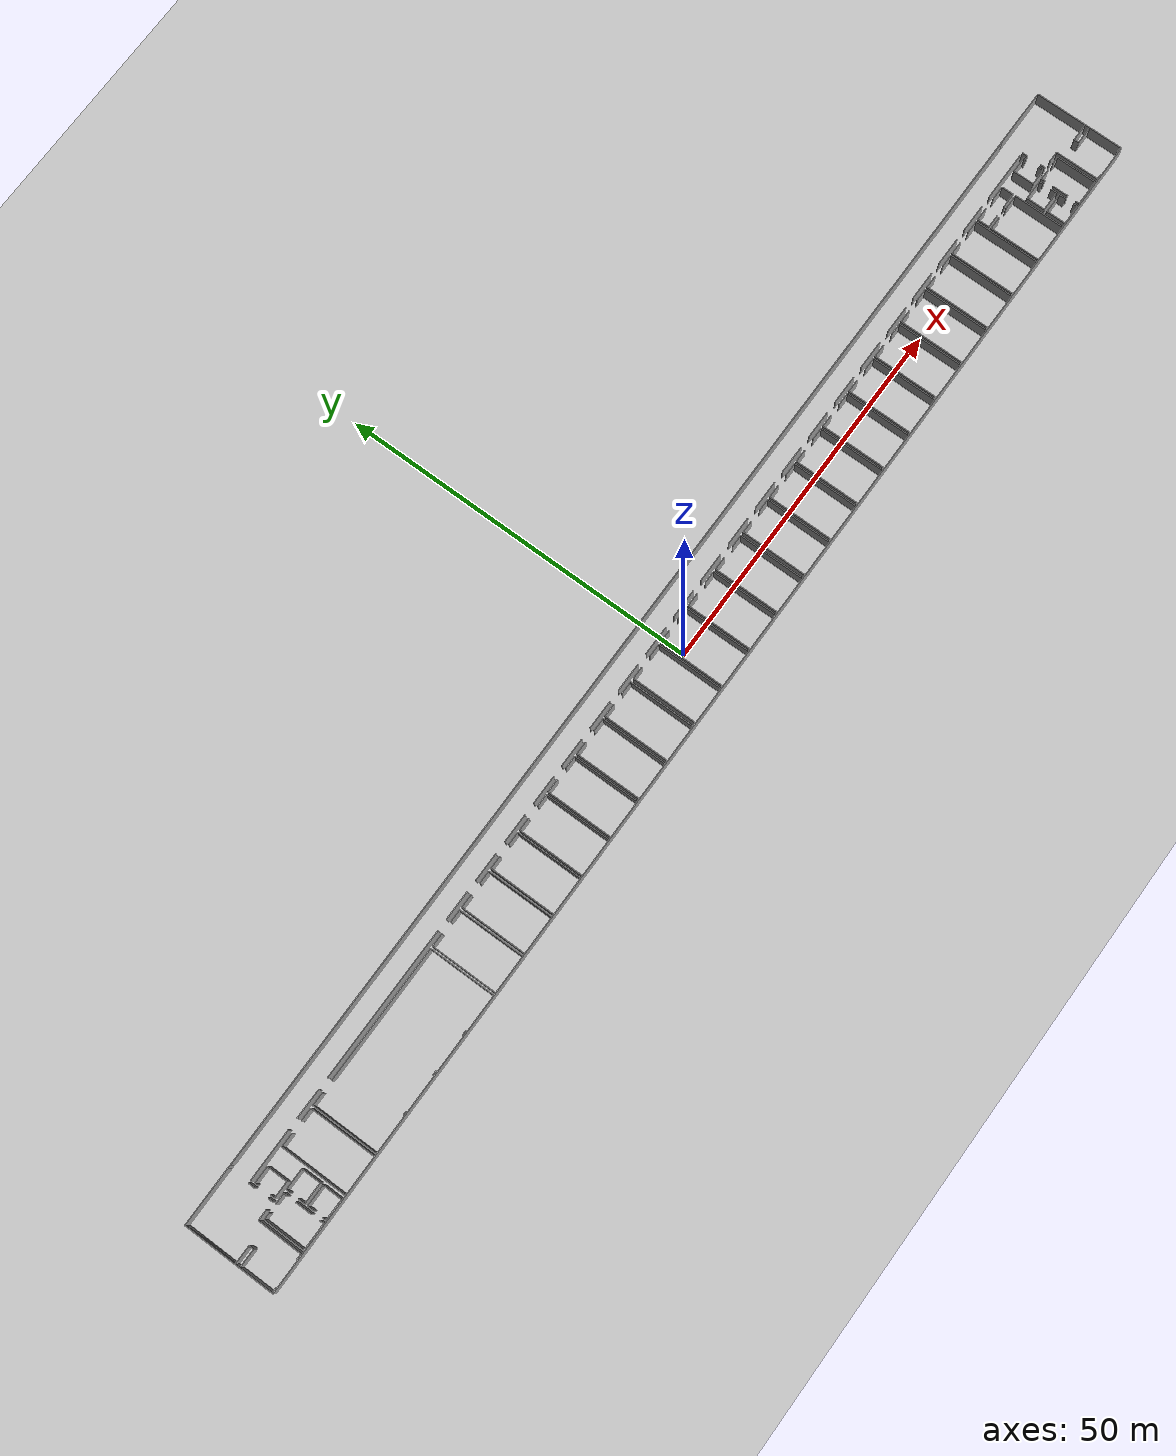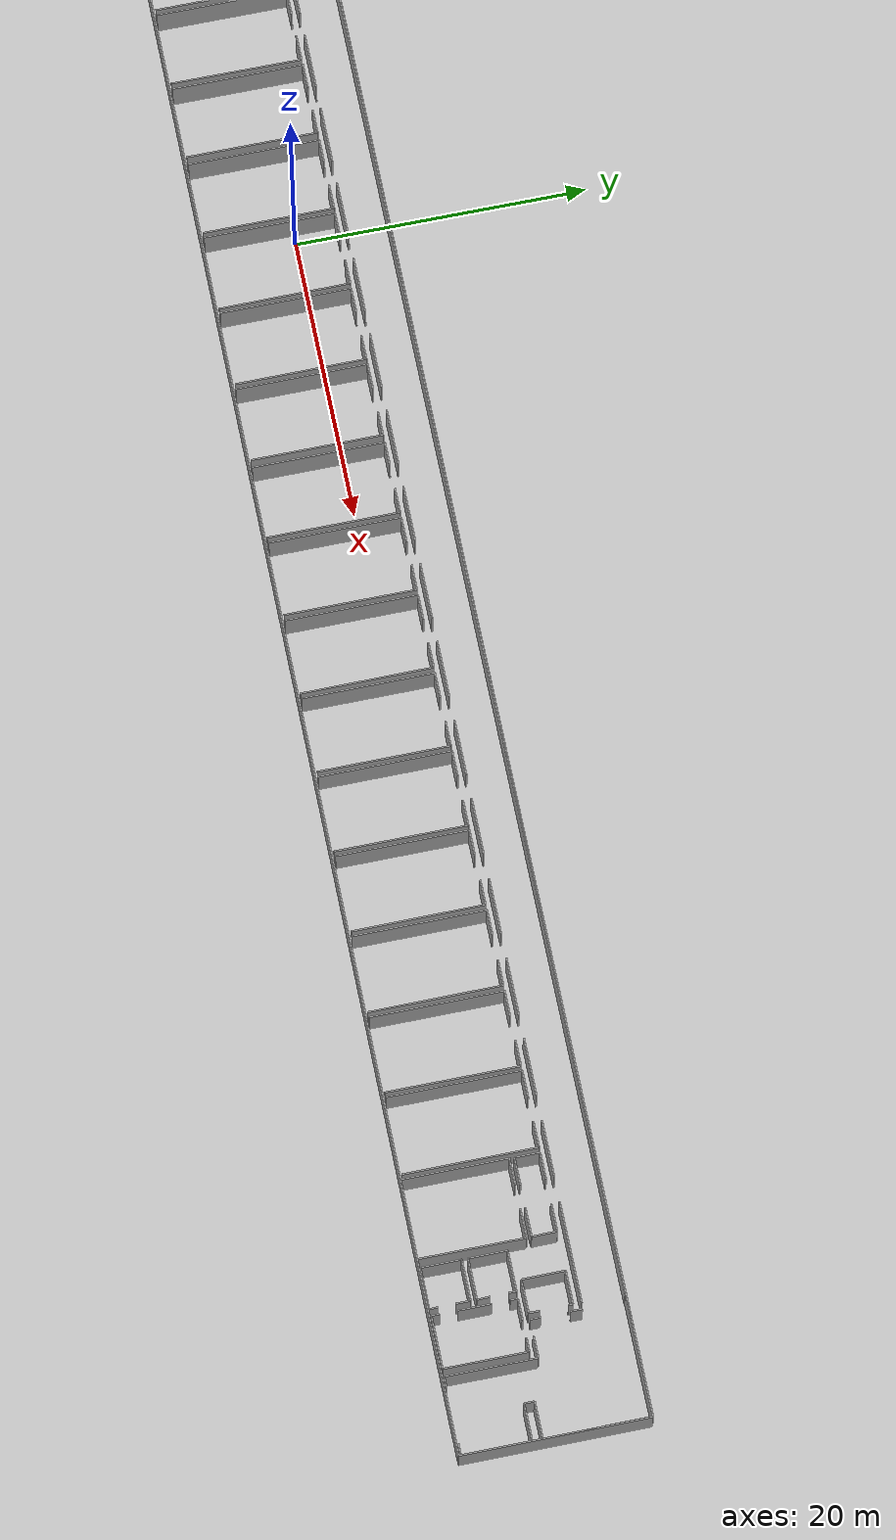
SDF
<sdf version="1.6">
  <world name="default">
    <light name="sun" type="directional">
      <cast_shadows>1</cast_shadows>
      <pose frame="">0 0 10 0 -0 0</pose>
      <diffuse>0.8 0.8 0.8 1</diffuse>
      <specular>0.1 0.1 0.1 1</specular>
      <attenuation>
        <range>1000</range>
        <constant>0.9</constant>
        <linear>0.01</linear>
        <quadratic>0.001</quadratic>
      </attenuation>
      <direction>-0.5 0.5 -1</direction>
    </light>
    <model name="ground_plane">
      <static>1</static>
      <link name="link">
        <collision name="collision">
          <geometry>
            <plane>
              <normal>0 0 1</normal>
              <size>100 100</size>
            </plane>
          </geometry>
          <surface>
            <friction>
              <ode>
                <mu>100</mu>
                <mu2>50</mu2>
              </ode>
              <torsional>
                <ode />
              </torsional>
            </friction>
            <contact>
              <ode />
            </contact>
            <bounce />
          </surface>
          <max_contacts>10</max_contacts>
        </collision>
        <visual name="visual">
          <cast_shadows>0</cast_shadows>
          <geometry>
            <plane>
              <normal>0 0 1</normal>
              <size>100 100</size>
            </plane>
          </geometry>
          <material>
            <script>
              <uri>file://media/materials/scripts/gazebo.material</uri>
              <name>Gazebo/Grey</name>
            </script>
          </material>
        </visual>
        <self_collide>0</self_collide>
        <kinematic>0</kinematic>
        <gravity>1</gravity>
      </link>
    </model>
    <gravity>0 0 -9.8</gravity>
    <magnetic_field>6e-06 2.3e-05 -4.2e-05</magnetic_field>
    <atmosphere type="adiabatic" />
    <physics default="0" name="default_physics" type="ode">
      <max_step_size>0.001</max_step_size>
      <real_time_factor>1</real_time_factor>
      <real_time_update_rate>1000</real_time_update_rate>
    </physics>
    <scene>
      <ambient>0.4 0.4 0.4 1</ambient>
      <background>0.7 0.7 0.7 1</background>
      <shadows>1</shadows>
    </scene>
    <spherical_coordinates>
      <surface_model>EARTH_WGS84</surface_model>
      <latitude_deg>0</latitude_deg>
      <longitude_deg>0</longitude_deg>
      <elevation>0</elevation>
      <heading_deg>0</heading_deg>
    </spherical_coordinates>
  <model name="50015850_PLAN5">
		<static>1</static>
		<link name="Wall_0">
			<collision name="Wall_0_Collision">
				<geometry>
					<box>
						<size>155.368060402 0.1 2.5</size>
					</box>
				</geometry>
				<pose frame="">77.6840302011 0 1.25 0 0 0</pose>
			</collision>
			<visual name="Wall_0_Visual">
				<pose frame="">77.6840302011 0 1.25 0 0 0</pose>
				<geometry>
					<box>
						<size>155.368060402 0.1 2.5</size>
					</box>
				</geometry>
				<material>
					<script>
						<uri>file://media/materials/scripts/gazebo.material</uri>
						<name>Gazebo/Grey</name>
					</script>
					<ambient>1 1 1 1</ambient>
				</material>
			</visual>
			<pose frame="">8.18019161221 -0.0307848486771 0 0 0 0.0</pose>
		</link>
		<link name="Wall_1">
			<collision name="Wall_1_Collision">
				<geometry>
					<box>
						<size>6.90260770256 0.1 2.5</size>
					</box>
				</geometry>
				<pose frame="">3.45130385128 0 1.25 0 0 0</pose>
			</collision>
			<visual name="Wall_1_Visual">
				<pose frame="">3.45130385128 0 1.25 0 0 0</pose>
				<geometry>
					<box>
						<size>6.90260770256 0.1 2.5</size>
					</box>
				</geometry>
				<material>
					<script>
						<uri>file://media/materials/scripts/gazebo.material</uri>
						<name>Gazebo/Grey</name>
					</script>
					<ambient>1 1 1 1</ambient>
				</material>
			</visual>
			<pose frame="">163.548252014 -2.89976524332 0 0 0 3.14159265359</pose>
		</link>
		<link name="Wall_2">
			<collision name="Wall_2_Collision">
				<geometry>
					<box>
						<size>3.93909015925 0.1 2.5</size>
					</box>
				</geometry>
				<pose frame="">1.96954507963 0 1.25 0 0 0</pose>
			</collision>
			<visual name="Wall_2_Visual">
				<pose frame="">1.96954507963 0 1.25 0 0 0</pose>
				<geometry>
					<box>
						<size>3.93909015925 0.1 2.5</size>
					</box>
				</geometry>
				<material>
					<script>
						<uri>file://media/materials/scripts/gazebo.material</uri>
						<name>Gazebo/Grey</name>
					</script>
					<ambient>1 1 1 1</ambient>
				</material>
			</visual>
			<pose frame="">155.024681175 -2.89976524332 0 0 0 3.14159265359</pose>
		</link>
		<link name="Wall_3">
			<collision name="Wall_3_Collision">
				<geometry>
					<box>
						<size>4.01954190724 0.1 2.5</size>
					</box>
				</geometry>
				<pose frame="">2.00977095362 0 1.25 0 0 0</pose>
			</collision>
			<visual name="Wall_3_Visual">
				<pose frame="">2.00977095362 0 1.25 0 0 0</pose>
				<geometry>
					<box>
						<size>4.01954190724 0.1 2.5</size>
					</box>
				</geometry>
				<material>
					<script>
						<uri>file://media/materials/scripts/gazebo.material</uri>
						<name>Gazebo/Grey</name>
					</script>
					<ambient>1 1 1 1</ambient>
				</material>
			</visual>
			<pose frame="">149.454222448 -2.89976524332 0 0 0 3.14159265359</pose>
		</link>
		<link name="Wall_4">
			<collision name="Wall_4_Collision">
				<geometry>
					<box>
						<size>3.9758898547 0.1 2.5</size>
					</box>
				</geometry>
				<pose frame="">1.98794492735 0 1.25 0 0 0</pose>
			</collision>
			<visual name="Wall_4_Visual">
				<pose frame="">1.98794492735 0 1.25 0 0 0</pose>
				<geometry>
					<box>
						<size>3.9758898547 0.1 2.5</size>
					</box>
				</geometry>
				<material>
					<script>
						<uri>file://media/materials/scripts/gazebo.material</uri>
						<name>Gazebo/Grey</name>
					</script>
					<ambient>1 1 1 1</ambient>
				</material>
			</visual>
			<pose frame="">143.853055009 -2.89976524332 0 0 0 3.14159265359</pose>
		</link>
		<link name="Wall_5">
			<collision name="Wall_5_Collision">
				<geometry>
					<box>
						<size>3.92969989214 0.1 2.5</size>
					</box>
				</geometry>
				<pose frame="">1.96484994607 0 1.25 0 0 0</pose>
			</collision>
			<visual name="Wall_5_Visual">
				<pose frame="">1.96484994607 0 1.25 0 0 0</pose>
				<geometry>
					<box>
						<size>3.92969989214 0.1 2.5</size>
					</box>
				</geometry>
				<material>
					<script>
						<uri>file://media/materials/scripts/gazebo.material</uri>
						<name>Gazebo/Grey</name>
					</script>
					<ambient>1 1 1 1</ambient>
				</material>
			</visual>
			<pose frame="">138.263815748 -2.89976524332 0 0 0 3.14159265359</pose>
		</link>
		<link name="Wall_6">
			<collision name="Wall_6_Collision">
				<geometry>
					<box>
						<size>3.97766639173 0.1 2.5</size>
					</box>
				</geometry>
				<pose frame="">1.98883319586 0 1.25 0 0 0</pose>
			</collision>
			<visual name="Wall_6_Visual">
				<pose frame="">1.98883319586 0 1.25 0 0 0</pose>
				<geometry>
					<box>
						<size>3.97766639173 0.1 2.5</size>
					</box>
				</geometry>
				<material>
					<script>
						<uri>file://media/materials/scripts/gazebo.material</uri>
						<name>Gazebo/Grey</name>
					</script>
					<ambient>1 1 1 1</ambient>
				</material>
			</visual>
			<pose frame="">132.636254045 -2.89976524332 0 0 0 3.14159265359</pose>
		</link>
		<link name="Wall_7">
			<collision name="Wall_7_Collision">
				<geometry>
					<box>
						<size>3.93249159317 0.1 2.5</size>
					</box>
				</geometry>
				<pose frame="">1.96624579659 0 1.25 0 0 0</pose>
			</collision>
			<visual name="Wall_7_Visual">
				<pose frame="">1.96624579659 0 1.25 0 0 0</pose>
				<geometry>
					<box>
						<size>3.93249159317 0.1 2.5</size>
					</box>
				</geometry>
				<material>
					<script>
						<uri>file://media/materials/scripts/gazebo.material</uri>
						<name>Gazebo/Grey</name>
					</script>
					<ambient>1 1 1 1</ambient>
				</material>
			</visual>
			<pose frame="">127.035340397 -2.89976524332 0 0 0 3.14159265359</pose>
		</link>
		<link name="Wall_8">
			<collision name="Wall_8_Collision">
				<geometry>
					<box>
						<size>3.96142376753 0.1 2.5</size>
					</box>
				</geometry>
				<pose frame="">1.98071188376 0 1.25 0 0 0</pose>
			</collision>
			<visual name="Wall_8_Visual">
				<pose frame="">1.98071188376 0 1.25 0 0 0</pose>
				<geometry>
					<box>
						<size>3.96142376753 0.1 2.5</size>
					</box>
				</geometry>
				<material>
					<script>
						<uri>file://media/materials/scripts/gazebo.material</uri>
						<name>Gazebo/Grey</name>
					</script>
					<ambient>1 1 1 1</ambient>
				</material>
			</visual>
			<pose frame="">121.448639046 -2.89976524332 0 0 0 3.14159265359</pose>
		</link>
		<link name="Wall_9">
			<collision name="Wall_9_Collision">
				<geometry>
					<box>
						<size>3.96446925956 0.1 2.5</size>
					</box>
				</geometry>
				<pose frame="">1.98223462978 0 1.25 0 0 0</pose>
			</collision>
			<visual name="Wall_9_Visual">
				<pose frame="">1.98223462978 0 1.25 0 0 0</pose>
				<geometry>
					<box>
						<size>3.96446925956 0.1 2.5</size>
					</box>
				</geometry>
				<material>
					<script>
						<uri>file://media/materials/scripts/gazebo.material</uri>
						<name>Gazebo/Grey</name>
					</script>
					<ambient>1 1 1 1</ambient>
				</material>
			</visual>
			<pose frame="">115.868790051 -2.89976524332 0 0 0 3.14159265359</pose>
		</link>
		<link name="Wall_10">
			<collision name="Wall_10_Collision">
				<geometry>
					<box>
						<size>3.97157540765 0.1 2.5</size>
					</box>
				</geometry>
				<pose frame="">1.98578770383 0 1.25 0 0 0</pose>
			</collision>
			<visual name="Wall_10_Visual">
				<pose frame="">1.98578770383 0 1.25 0 0 0</pose>
				<geometry>
					<box>
						<size>3.97157540765 0.1 2.5</size>
					</box>
				</geometry>
				<material>
					<script>
						<uri>file://media/materials/scripts/gazebo.material</uri>
						<name>Gazebo/Grey</name>
					</script>
					<ambient>1 1 1 1</ambient>
				</material>
			</visual>
			<pose frame="">110.282850073 -2.89976524332 0 0 0 3.14159265359</pose>
		</link>
		<link name="Wall_11">
			<collision name="Wall_11_Collision">
				<geometry>
					<box>
						<size>3.96142376753 0.1 2.5</size>
					</box>
				</geometry>
				<pose frame="">1.98071188376 0 1.25 0 0 0</pose>
			</collision>
			<visual name="Wall_11_Visual">
				<pose frame="">1.98071188376 0 1.25 0 0 0</pose>
				<geometry>
					<box>
						<size>3.96142376753 0.1 2.5</size>
					</box>
				</geometry>
				<material>
					<script>
						<uri>file://media/materials/scripts/gazebo.material</uri>
						<name>Gazebo/Grey</name>
					</script>
					<ambient>1 1 1 1</ambient>
				</material>
			</visual>
			<pose frame="">104.674576486 -2.89976524332 0 0 0 3.14159265359</pose>
		</link>
		<link name="Wall_12">
			<collision name="Wall_12_Collision">
				<geometry>
					<box>
						<size>3.95837827549 0.1 2.5</size>
					</box>
				</geometry>
				<pose frame="">1.97918913775 0 1.25 0 0 0</pose>
			</collision>
			<visual name="Wall_12_Visual">
				<pose frame="">1.97918913775 0 1.25 0 0 0</pose>
				<geometry>
					<box>
						<size>3.95837827549 0.1 2.5</size>
					</box>
				</geometry>
				<material>
					<script>
						<uri>file://media/materials/scripts/gazebo.material</uri>
						<name>Gazebo/Grey</name>
					</script>
					<ambient>1 1 1 1</ambient>
				</material>
			</visual>
			<pose frame="">99.0444768733 -2.89976524332 0 0 0 3.14159265359</pose>
		</link>
		<link name="Wall_13">
			<collision name="Wall_13_Collision">
				<geometry>
					<box>
						<size>4.01573504219 0.1 2.5</size>
					</box>
				</geometry>
				<pose frame="">2.0078675211 0 1.25 0 0 0</pose>
			</collision>
			<visual name="Wall_13_Visual">
				<pose frame="">2.0078675211 0 1.25 0 0 0</pose>
				<geometry>
					<box>
						<size>4.01573504219 0.1 2.5</size>
					</box>
				</geometry>
				<material>
					<script>
						<uri>file://media/materials/scripts/gazebo.material</uri>
						<name>Gazebo/Grey</name>
					</script>
					<ambient>1 1 1 1</ambient>
				</material>
			</visual>
			<pose frame="">93.5151322886 -2.89976524332 0 0 0 3.14159265359</pose>
		</link>
		<link name="Wall_14">
			<collision name="Wall_14_Collision">
				<geometry>
					<box>
						<size>3.96193134953 0.1 2.5</size>
					</box>
				</geometry>
				<pose frame="">1.98096567477 0 1.25 0 0 0</pose>
			</collision>
			<visual name="Wall_14_Visual">
				<pose frame="">1.98096567477 0 1.25 0 0 0</pose>
				<geometry>
					<box>
						<size>3.96193134953 0.1 2.5</size>
					</box>
				</geometry>
				<material>
					<script>
						<uri>file://media/materials/scripts/gazebo.material</uri>
						<name>Gazebo/Grey</name>
					</script>
					<ambient>1 1 1 1</ambient>
				</material>
			</visual>
			<pose frame="">87.8654907684 -2.89976524332 0 0 0 3.14159265359</pose>
		</link>
		<link name="Wall_15">
			<collision name="Wall_15_Collision">
				<geometry>
					<box>
						<size>3.96142376753 0.1 2.5</size>
					</box>
				</geometry>
				<pose frame="">1.98071188376 0 1.25 0 0 0</pose>
			</collision>
			<visual name="Wall_15_Visual">
				<pose frame="">1.98071188376 0 1.25 0 0 0</pose>
				<geometry>
					<box>
						<size>3.96142376753 0.1 2.5</size>
					</box>
				</geometry>
				<material>
					<script>
						<uri>file://media/materials/scripts/gazebo.material</uri>
						<name>Gazebo/Grey</name>
					</script>
					<ambient>1 1 1 1</ambient>
				</material>
			</visual>
			<pose frame="">82.2556944356 -2.89976524332 0 0 0 3.14159265359</pose>
		</link>
		<link name="Wall_16">
			<collision name="Wall_16_Collision">
				<geometry>
					<box>
						<size>3.99390901593 0.1 2.5</size>
					</box>
				</geometry>
				<pose frame="">1.99695450796 0 1.25 0 0 0</pose>
			</collision>
			<visual name="Wall_16_Visual">
				<pose frame="">1.99695450796 0 1.25 0 0 0</pose>
				<geometry>
					<box>
						<size>3.99390901593 0.1 2.5</size>
					</box>
				</geometry>
				<material>
					<script>
						<uri>file://media/materials/scripts/gazebo.material</uri>
						<name>Gazebo/Grey</name>
					</script>
					<ambient>1 1 1 1</ambient>
				</material>
			</visual>
			<pose frame="">76.6948797665 -2.89976524332 0 0 0 3.14159265359</pose>
		</link>
		<link name="Wall_17">
			<collision name="Wall_17_Collision">
				<geometry>
					<box>
						<size>3.9758898547 0.1 2.5</size>
					</box>
				</geometry>
				<pose frame="">1.98794492735 0 1.25 0 0 0</pose>
			</collision>
			<visual name="Wall_17_Visual">
				<pose frame="">1.98794492735 0 1.25 0 0 0</pose>
				<geometry>
					<box>
						<size>3.9758898547 0.1 2.5</size>
					</box>
				</geometry>
				<material>
					<script>
						<uri>file://media/materials/scripts/gazebo.material</uri>
						<name>Gazebo/Grey</name>
					</script>
					<ambient>1 1 1 1</ambient>
				</material>
			</visual>
			<pose frame="">71.0680794366 -2.89976524332 0 0 0 3.14159265359</pose>
		</link>
		<link name="Wall_18">
			<collision name="Wall_18_Collision">
				<geometry>
					<box>
						<size>3.91777171499 0.1 2.5</size>
					</box>
				</geometry>
				<pose frame="">1.9588858575 0 1.25 0 0 0</pose>
			</collision>
			<visual name="Wall_18_Visual">
				<pose frame="">1.9588858575 0 1.25 0 0 0</pose>
				<geometry>
					<box>
						<size>3.91777171499 0.1 2.5</size>
					</box>
				</geometry>
				<material>
					<script>
						<uri>file://media/materials/scripts/gazebo.material</uri>
						<name>Gazebo/Grey</name>
					</script>
					<ambient>1 1 1 1</ambient>
				</material>
			</visual>
			<pose frame="">65.4958441723 -2.89976524332 0 0 0 3.14159265359</pose>
		</link>
		<link name="Wall_19">
			<collision name="Wall_19_Collision">
				<geometry>
					<box>
						<size>3.92132478904 0.1 2.5</size>
					</box>
				</geometry>
				<pose frame="">1.96066239452 0 1.25 0 0 0</pose>
			</collision>
			<visual name="Wall_19_Visual">
				<pose frame="">1.96066239452 0 1.25 0 0 0</pose>
				<geometry>
					<box>
						<size>3.92132478904 0.1 2.5</size>
					</box>
				</geometry>
				<material>
					<script>
						<uri>file://media/materials/scripts/gazebo.material</uri>
						<name>Gazebo/Grey</name>
					</script>
					<ambient>1 1 1 1</ambient>
				</material>
			</visual>
			<pose frame="">59.8708203794 -2.89976524332 0 0 0 3.14159265359</pose>
		</link>
		<link name="Wall_20">
			<collision name="Wall_20_Collision">
				<geometry>
					<box>
						<size>3.92157858004 0.1 2.5</size>
					</box>
				</geometry>
				<pose frame="">1.96078929002 0 1.25 0 0 0</pose>
			</collision>
			<visual name="Wall_20_Visual">
				<pose frame="">1.96078929002 0 1.25 0 0 0</pose>
				<geometry>
					<box>
						<size>3.92157858004 0.1 2.5</size>
					</box>
				</geometry>
				<material>
					<script>
						<uri>file://media/materials/scripts/gazebo.material</uri>
						<name>Gazebo/Grey</name>
					</script>
					<ambient>1 1 1 1</ambient>
				</material>
			</visual>
			<pose frame="">54.2105196371 -2.89976524332 0 0 0 3.14159265359</pose>
		</link>
		<link name="Wall_21">
			<collision name="Wall_21_Collision">
				<geometry>
					<box>
						<size>4.02157223526 0.1 2.5</size>
					</box>
				</geometry>
				<pose frame="">2.01078611763 0 1.25 0 0 0</pose>
			</collision>
			<visual name="Wall_21_Visual">
				<pose frame="">2.01078611763 0 1.25 0 0 0</pose>
				<geometry>
					<box>
						<size>4.02157223526 0.1 2.5</size>
					</box>
				</geometry>
				<material>
					<script>
						<uri>file://media/materials/scripts/gazebo.material</uri>
						<name>Gazebo/Grey</name>
					</script>
					<ambient>1 1 1 1</ambient>
				</material>
			</visual>
			<pose frame="">48.7070617347 -2.89976524332 0 0 0 3.14159265359</pose>
		</link>
		<link name="Wall_22">
			<collision name="Wall_22_Collision">
				<geometry>
					<box>
						<size>20.818729776 0.1 2.5</size>
					</box>
				</geometry>
				<pose frame="">10.409364888 0 1.25 0 0 0</pose>
			</collision>
			<visual name="Wall_22_Visual">
				<pose frame="">10.409364888 0 1.25 0 0 0</pose>
				<geometry>
					<box>
						<size>20.818729776 0.1 2.5</size>
					</box>
				</geometry>
				<material>
					<script>
						<uri>file://media/materials/scripts/gazebo.material</uri>
						<name>Gazebo/Grey</name>
					</script>
					<ambient>1 1 1 1</ambient>
				</material>
			</visual>
			<pose frame="">43.1350802614 -2.89976524332 0 0 0 3.14159265359</pose>
		</link>
		<link name="Wall_23">
			<collision name="Wall_23_Collision">
				<geometry>
					<box>
						<size>4.01928811624 0.1 2.5</size>
					</box>
				</geometry>
				<pose frame="">2.00964405812 0 1.25 0 0 0</pose>
			</collision>
			<visual name="Wall_23_Visual">
				<pose frame="">2.00964405812 0 1.25 0 0 0</pose>
				<geometry>
					<box>
						<size>4.01928811624 0.1 2.5</size>
					</box>
				</geometry>
				<material>
					<script>
						<uri>file://media/materials/scripts/gazebo.material</uri>
						<name>Gazebo/Grey</name>
					</script>
					<ambient>1 1 1 1</ambient>
				</material>
			</visual>
			<pose frame="">20.730664298 -2.89976524332 0 0 0 3.14159265359</pose>
		</link>
		<link name="Wall_24">
			<collision name="Wall_24_Collision">
				<geometry>
					<box>
						<size>6.96914460468 0.1 2.5</size>
					</box>
				</geometry>
				<pose frame="">3.48457230234 0 1.25 0 0 0</pose>
			</collision>
			<visual name="Wall_24_Visual">
				<pose frame="">3.48457230234 0 1.25 0 0 0</pose>
				<geometry>
					<box>
						<size>6.96914460468 0.1 2.5</size>
					</box>
				</geometry>
				<material>
					<script>
						<uri>file://media/materials/scripts/gazebo.material</uri>
						<name>Gazebo/Grey</name>
					</script>
					<ambient>1 1 1 1</ambient>
				</material>
			</visual>
			<pose frame="">15.1492925576 -2.89976524332 0 0 0 -3.13805297427</pose>
		</link>
		<link name="Wall_25">
			<collision name="Wall_25_Collision">
				<geometry>
					<box>
						<size>0.744369012119 0.1 2.5</size>
					</box>
				</geometry>
				<pose frame="">0.372184506059 0 1.25 0 0 0</pose>
			</collision>
			<visual name="Wall_25_Visual">
				<pose frame="">0.372184506059 0 1.25 0 0 0</pose>
				<geometry>
					<box>
						<size>0.744369012119 0.1 2.5</size>
					</box>
				</geometry>
				<material>
					<script>
						<uri>file://media/materials/scripts/gazebo.material</uri>
						<name>Gazebo/Grey</name>
					</script>
					<ambient>1 1 1 1</ambient>
				</material>
			</visual>
			<pose frame="">5.24357591523 -12.5019986041 0 0 0 3.14159265359</pose>
		</link>
		<link name="Wall_26">
			<collision name="Wall_26_Collision">
				<geometry>
					<box>
						<size>0.719243702811 0.1 2.5</size>
					</box>
				</geometry>
				<pose frame="">0.359621851405 0 1.25 0 0 0</pose>
			</collision>
			<visual name="Wall_26_Visual">
				<pose frame="">0.359621851405 0 1.25 0 0 0</pose>
				<geometry>
					<box>
						<size>0.719243702811 0.1 2.5</size>
					</box>
				</geometry>
				<material>
					<script>
						<uri>file://media/materials/scripts/gazebo.material</uri>
						<name>Gazebo/Grey</name>
					</script>
					<ambient>1 1 1 1</ambient>
				</material>
			</visual>
			<pose frame="">0.726349850898 -12.5019986041 0 0 0 3.14159265359</pose>
		</link>
		<link name="Wall_27">
			<collision name="Wall_27_Collision">
				<geometry>
					<box>
						<size>4.60678890933 0.1 2.5</size>
					</box>
				</geometry>
				<pose frame="">2.30339445467 0 1.25 0 0 0</pose>
			</collision>
			<visual name="Wall_27_Visual">
				<pose frame="">2.30339445467 0 1.25 0 0 0</pose>
				<geometry>
					<box>
						<size>4.60678890933 0.1 2.5</size>
					</box>
				</geometry>
				<material>
					<script>
						<uri>file://media/materials/scripts/gazebo.material</uri>
						<name>Gazebo/Grey</name>
					</script>
					<ambient>1 1 1 1</ambient>
				</material>
			</visual>
			<pose frame="">0.00710614808705 -12.5019986041 0 0 0 1.57079632679</pose>
		</link>
		<link name="Wall_28">
			<collision name="Wall_28_Collision">
				<geometry>
					<box>
						<size>2.50542478269 0.1 2.5</size>
					</box>
				</geometry>
				<pose frame="">1.25271239135 0 1.25 0 0 0</pose>
			</collision>
			<visual name="Wall_28_Visual">
				<pose frame="">1.25271239135 0 1.25 0 0 0</pose>
				<geometry>
					<box>
						<size>2.50542478269 0.1 2.5</size>
					</box>
				</geometry>
				<material>
					<script>
						<uri>file://media/materials/scripts/gazebo.material</uri>
						<name>Gazebo/Grey</name>
					</script>
					<ambient>1 1 1 1</ambient>
				</material>
			</visual>
			<pose frame="">0.00710614808705 -7.89520969482 0 0 0 0.0</pose>
		</link>
		<link name="Wall_29">
			<collision name="Wall_29_Collision">
				<geometry>
					<box>
						<size>0.66366347313 0.1 2.5</size>
					</box>
				</geometry>
				<pose frame="">0.331831736565 0 1.25 0 0 0</pose>
			</collision>
			<visual name="Wall_29_Visual">
				<pose frame="">0.331831736565 0 1.25 0 0 0</pose>
				<geometry>
					<box>
						<size>0.66366347313 0.1 2.5</size>
					</box>
				</geometry>
				<material>
					<script>
						<uri>file://media/materials/scripts/gazebo.material</uri>
						<name>Gazebo/Grey</name>
					</script>
					<ambient>1 1 1 1</ambient>
				</material>
			</visual>
			<pose frame="">2.51253093078 -7.89520969482 0 0 0 1.57079632679</pose>
		</link>
		<link name="Wall_30">
			<collision name="Wall_30_Collision">
				<geometry>
					<box>
						<size>2.51253093078 0.1 2.5</size>
					</box>
				</geometry>
				<pose frame="">1.25626546539 0 1.25 0 0 0</pose>
			</collision>
			<visual name="Wall_30_Visual">
				<pose frame="">1.25626546539 0 1.25 0 0 0</pose>
				<geometry>
					<box>
						<size>2.51253093078 0.1 2.5</size>
					</box>
				</geometry>
				<material>
					<script>
						<uri>file://media/materials/scripts/gazebo.material</uri>
						<name>Gazebo/Grey</name>
					</script>
					<ambient>1 1 1 1</ambient>
				</material>
			</visual>
			<pose frame="">2.51253093078 -7.23154622169 0 0 0 3.14159265359</pose>
		</link>
		<link name="Wall_31">
			<collision name="Wall_31_Collision">
				<geometry>
					<box>
						<size>7.22773935664 0.1 2.5</size>
					</box>
				</geometry>
				<pose frame="">3.61386967832 0 1.25 0 0 0</pose>
			</collision>
			<visual name="Wall_31_Visual">
				<pose frame="">3.61386967832 0 1.25 0 0 0</pose>
				<geometry>
					<box>
						<size>7.22773935664 0.1 2.5</size>
					</box>
				</geometry>
				<material>
					<script>
						<uri>file://media/materials/scripts/gazebo.material</uri>
						<name>Gazebo/Grey</name>
					</script>
					<ambient>1 1 1 1</ambient>
				</material>
			</visual>
			<pose frame="">0.0 -7.23154622169 0 0 0 1.57079632679</pose>
		</link>
		<link name="Wall_32">
			<collision name="Wall_32_Collision">
				<geometry>
					<box>
						<size>7.83884271303 0.1 2.5</size>
					</box>
				</geometry>
				<pose frame="">3.91942135651 0 1.25 0 0 0</pose>
			</collision>
			<visual name="Wall_32_Visual">
				<pose frame="">3.91942135651 0 1.25 0 0 0</pose>
				<geometry>
					<box>
						<size>7.83884271303 0.1 2.5</size>
					</box>
				</geometry>
				<material>
					<script>
						<uri>file://media/materials/scripts/gazebo.material</uri>
						<name>Gazebo/Grey</name>
					</script>
					<ambient>1 1 1 1</ambient>
				</material>
			</visual>
			<pose frame="">0.0 -0.00380686504663 0 0 0 0.0</pose>
		</link>
		<link name="Wall_33">
			<collision name="Wall_33_Collision">
				<geometry>
					<box>
						<size>0.91593173022 0.1 2.5</size>
					</box>
				</geometry>
				<pose frame="">0.45796586511 0 1.25 0 0 0</pose>
			</collision>
			<visual name="Wall_33_Visual">
				<pose frame="">0.45796586511 0 1.25 0 0 0</pose>
				<geometry>
					<box>
						<size>0.91593173022 0.1 2.5</size>
					</box>
				</geometry>
				<material>
					<script>
						<uri>file://media/materials/scripts/gazebo.material</uri>
						<name>Gazebo/Grey</name>
					</script>
					<ambient>1 1 1 1</ambient>
				</material>
			</visual>
			<pose frame="">7.83884271303 -2.85654463549 0 0 0 -1.57079632679</pose>
		</link>
		<link name="Wall_34">
			<collision name="Wall_34_Collision">
				<geometry>
					<box>
						<size>0.652978871899 0.1 2.5</size>
					</box>
				</geometry>
				<pose frame="">0.326489435949 0 1.25 0 0 0</pose>
			</collision>
			<visual name="Wall_34_Visual">
				<pose frame="">0.326489435949 0 1.25 0 0 0</pose>
				<geometry>
					<box>
						<size>0.652978871899 0.1 2.5</size>
					</box>
				</geometry>
				<material>
					<script>
						<uri>file://media/materials/scripts/gazebo.material</uri>
						<name>Gazebo/Grey</name>
					</script>
					<ambient>1 1 1 1</ambient>
				</material>
			</visual>
			<pose frame="">7.83884271303 -5.71862191485 0 0 0 -1.57079632679</pose>
		</link>
		<link name="Wall_35">
			<collision name="Wall_35_Collision">
				<geometry>
					<box>
						<size>1.43848740562 0.1 2.5</size>
					</box>
				</geometry>
				<pose frame="">0.719243702811 0 1.25 0 0 0</pose>
			</collision>
			<visual name="Wall_35_Visual">
				<pose frame="">0.719243702811 0 1.25 0 0 0</pose>
				<geometry>
					<box>
						<size>1.43848740562 0.1 2.5</size>
					</box>
				</geometry>
				<material>
					<script>
						<uri>file://media/materials/scripts/gazebo.material</uri>
						<name>Gazebo/Grey</name>
					</script>
					<ambient>1 1 1 1</ambient>
				</material>
			</visual>
			<pose frame="">6.71987818032 -6.37160078675 0 0 0 3.14159265359</pose>
		</link>
		<link name="Wall_36">
			<collision name="Wall_36_Collision">
				<geometry>
					<box>
						<size>6.13051444523 0.1 2.5</size>
					</box>
				</geometry>
				<pose frame="">3.06525722261 0 1.25 0 0 0</pose>
			</collision>
			<visual name="Wall_36_Visual">
				<pose frame="">3.06525722261 0 1.25 0 0 0</pose>
				<geometry>
					<box>
						<size>6.13051444523 0.1 2.5</size>
					</box>
				</geometry>
				<material>
					<script>
						<uri>file://media/materials/scripts/gazebo.material</uri>
						<name>Gazebo/Grey</name>
					</script>
					<ambient>1 1 1 1</ambient>
				</material>
			</visual>
			<pose frame="">5.2813907747 -6.37160078675 0 0 0 -1.57696466709</pose>
		</link>
		<link name="Wall_37">
			<collision name="Wall_37_Collision">
				<geometry>
					<box>
						<size>3.65915868282 0.1 2.5</size>
					</box>
				</geometry>
				<pose frame="">1.82957934141 0 1.25 0 0 0</pose>
			</collision>
			<visual name="Wall_37_Visual">
				<pose frame="">1.82957934141 0 1.25 0 0 0</pose>
				<geometry>
					<box>
						<size>3.65915868282 0.1 2.5</size>
					</box>
				</geometry>
				<material>
					<script>
						<uri>file://media/materials/scripts/gazebo.material</uri>
						<name>Gazebo/Grey</name>
					</script>
					<ambient>1 1 1 1</ambient>
				</material>
			</visual>
			<pose frame="">9.38214580293 -12.5344838525 0 0 0 3.14159265359</pose>
		</link>
		<link name="Wall_38">
			<collision name="Wall_38_Collision">
				<geometry>
					<box>
						<size>5.70060275363 0.1 2.5</size>
					</box>
				</geometry>
				<pose frame="">2.85030137682 0 1.25 0 0 0</pose>
			</collision>
			<visual name="Wall_38_Visual">
				<pose frame="">2.85030137682 0 1.25 0 0 0</pose>
				<geometry>
					<box>
						<size>5.70060275363 0.1 2.5</size>
					</box>
				</geometry>
				<material>
					<script>
						<uri>file://media/materials/scripts/gazebo.material</uri>
						<name>Gazebo/Grey</name>
					</script>
					<ambient>1 1 1 1</ambient>
				</material>
			</visual>
			<pose frame="">5.72298712011 -12.5344838525 0 0 0 1.57079632679</pose>
		</link>
		<link name="Wall_39">
			<collision name="Wall_39_Collision">
				<geometry>
					<box>
						<size>0.931159190407 0.1 2.5</size>
					</box>
				</geometry>
				<pose frame="">0.465579595203 0 1.25 0 0 0</pose>
			</collision>
			<visual name="Wall_39_Visual">
				<pose frame="">0.465579595203 0 1.25 0 0 0</pose>
				<geometry>
					<box>
						<size>0.931159190407 0.1 2.5</size>
					</box>
				</geometry>
				<material>
					<script>
						<uri>file://media/materials/scripts/gazebo.material</uri>
						<name>Gazebo/Grey</name>
					</script>
					<ambient>1 1 1 1</ambient>
				</material>
			</visual>
			<pose frame="">5.72298712011 -6.83388109892 0 0 0 0.0</pose>
		</link>
		<link name="Wall_40">
			<collision name="Wall_40_Collision">
				<geometry>
					<box>
						<size>1.48518495019 0.1 2.5</size>
					</box>
				</geometry>
				<pose frame="">0.742592475097 0 1.25 0 0 0</pose>
			</collision>
			<visual name="Wall_40_Visual">
				<pose frame="">0.742592475097 0 1.25 0 0 0</pose>
				<geometry>
					<box>
						<size>1.48518495019 0.1 2.5</size>
					</box>
				</geometry>
				<material>
					<script>
						<uri>file://media/materials/scripts/gazebo.material</uri>
						<name>Gazebo/Grey</name>
					</script>
					<ambient>1 1 1 1</ambient>
				</material>
			</visual>
			<pose frame="">7.84874056215 -6.83388109892 0 0 0 0.0</pose>
		</link>
		<link name="Wall_41">
			<collision name="Wall_41_Collision">
				<geometry>
					<box>
						<size>0.522682570903 0.1 2.5</size>
					</box>
				</geometry>
				<pose frame="">0.261341285451 0 1.25 0 0 0</pose>
			</collision>
			<visual name="Wall_41_Visual">
				<pose frame="">0.261341285451 0 1.25 0 0 0</pose>
				<geometry>
					<box>
						<size>0.522682570903 0.1 2.5</size>
					</box>
				</geometry>
				<material>
					<script>
						<uri>file://media/materials/scripts/gazebo.material</uri>
						<name>Gazebo/Grey</name>
					</script>
					<ambient>1 1 1 1</ambient>
				</material>
			</visual>
			<pose frame="">9.33392551234 -6.83388109892 0 0 0 -1.57079632679</pose>
		</link>
		<link name="Wall_42">
			<collision name="Wall_42_Collision">
				<geometry>
					<box>
						<size>2.27120106592 0.1 2.5</size>
					</box>
				</geometry>
				<pose frame="">1.13560053296 0 1.25 0 0 0</pose>
			</collision>
			<visual name="Wall_42_Visual">
				<pose frame="">1.13560053296 0 1.25 0 0 0</pose>
				<geometry>
					<box>
						<size>2.27120106592 0.1 2.5</size>
					</box>
				</geometry>
				<material>
					<script>
						<uri>file://media/materials/scripts/gazebo.material</uri>
						<name>Gazebo/Grey</name>
					</script>
					<ambient>1 1 1 1</ambient>
				</material>
			</visual>
			<pose frame="">9.33392551234 -8.52735232536 0 0 0 -1.57079632679</pose>
		</link>
		<link name="Wall_43">
			<collision name="Wall_43_Collision">
				<geometry>
					<box>
						<size>0.589754594356 0.1 2.5</size>
					</box>
				</geometry>
				<pose frame="">0.294877297178 0 1.25 0 0 0</pose>
			</collision>
			<visual name="Wall_43_Visual">
				<pose frame="">0.294877297178 0 1.25 0 0 0</pose>
				<geometry>
					<box>
						<size>0.589754594356 0.1 2.5</size>
					</box>
				</geometry>
				<material>
					<script>
						<uri>file://media/materials/scripts/gazebo.material</uri>
						<name>Gazebo/Grey</name>
					</script>
					<ambient>1 1 1 1</ambient>
				</material>
			</visual>
			<pose frame="">9.33392551234 -11.9467038893 0 0 0 -1.48894163554</pose>
		</link>
		<link name="Wall_44">
			<collision name="Wall_44_Collision">
				<geometry>
					<box>
						<size>2.27117568682 0.1 2.5</size>
					</box>
				</geometry>
				<pose frame="">1.13558784341 0 1.25 0 0 0</pose>
			</collision>
			<visual name="Wall_44_Visual">
				<pose frame="">1.13558784341 0 1.25 0 0 0</pose>
				<geometry>
					<box>
						<size>2.27117568682 0.1 2.5</size>
					</box>
				</geometry>
				<material>
					<script>
						<uri>file://media/materials/scripts/gazebo.material</uri>
						<name>Gazebo/Grey</name>
					</script>
					<ambient>1 1 1 1</ambient>
				</material>
			</visual>
			<pose frame="">10.5429858512 -6.31921832371 0 0 0 3.14159265359</pose>
		</link>
		<link name="Wall_45">
			<collision name="Wall_45_Collision">
				<geometry>
					<box>
						<size>0.643512467483 0.1 2.5</size>
					</box>
				</geometry>
				<pose frame="">0.321756233742 0 1.25 0 0 0</pose>
			</collision>
			<visual name="Wall_45_Visual">
				<pose frame="">0.321756233742 0 1.25 0 0 0</pose>
				<geometry>
					<box>
						<size>0.643512467483 0.1 2.5</size>
					</box>
				</geometry>
				<material>
					<script>
						<uri>file://media/materials/scripts/gazebo.material</uri>
						<name>Gazebo/Grey</name>
					</script>
					<ambient>1 1 1 1</ambient>
				</material>
			</visual>
			<pose frame="">8.27181016433 -6.31921832371 0 0 0 1.57079632679</pose>
		</link>
		<link name="Wall_46">
			<collision name="Wall_46_Collision">
				<geometry>
					<box>
						<size>0.283662204175 0.1 2.5</size>
					</box>
				</geometry>
				<pose frame="">0.141831102087 0 1.25 0 0 0</pose>
			</collision>
			<visual name="Wall_46_Visual">
				<pose frame="">0.141831102087 0 1.25 0 0 0</pose>
				<geometry>
					<box>
						<size>0.283662204175 0.1 2.5</size>
					</box>
				</geometry>
				<material>
					<script>
						<uri>file://media/materials/scripts/gazebo.material</uri>
						<name>Gazebo/Grey</name>
					</script>
					<ambient>1 1 1 1</ambient>
				</material>
			</visual>
			<pose frame="">8.27181016433 -3.771283548 0 0 0 1.57079632679</pose>
		</link>
		<link name="Wall_47">
			<collision name="Wall_47_Collision">
				<geometry>
					<box>
						<size>2.25797855466 0.1 2.5</size>
					</box>
				</geometry>
				<pose frame="">1.12898927733 0 1.25 0 0 0</pose>
			</collision>
			<visual name="Wall_47_Visual">
				<pose frame="">1.12898927733 0 1.25 0 0 0</pose>
				<geometry>
					<box>
						<size>2.25797855466 0.1 2.5</size>
					</box>
				</geometry>
				<material>
					<script>
						<uri>file://media/materials/scripts/gazebo.material</uri>
						<name>Gazebo/Grey</name>
					</script>
					<ambient>1 1 1 1</ambient>
				</material>
			</visual>
			<pose frame="">8.27181016433 -3.48762134382 0 0 0 0.0</pose>
		</link>
		<link name="Wall_48">
			<collision name="Wall_48_Collision">
				<geometry>
					<box>
						<size>2.83162773344 0.1 2.5</size>
					</box>
				</geometry>
				<pose frame="">1.41581386672 0 1.25 0 0 0</pose>
			</collision>
			<visual name="Wall_48_Visual">
				<pose frame="">1.41581386672 0 1.25 0 0 0</pose>
				<geometry>
					<box>
						<size>2.83162773344 0.1 2.5</size>
					</box>
				</geometry>
				<material>
					<script>
						<uri>file://media/materials/scripts/gazebo.material</uri>
						<name>Gazebo/Grey</name>
					</script>
					<ambient>1 1 1 1</ambient>
				</material>
			</visual>
			<pose frame="">10.529788719 -3.48762134382 0 0 0 -1.56613569299</pose>
		</link>
		<link name="Wall_49">
			<collision name="Wall_49_Collision">
				<geometry>
					<box>
						<size>2.86377767908 0.1 2.5</size>
					</box>
				</geometry>
				<pose frame="">1.43188883954 0 1.25 0 0 0</pose>
			</collision>
			<visual name="Wall_49_Visual">
				<pose frame="">1.43188883954 0 1.25 0 0 0</pose>
				<geometry>
					<box>
						<size>2.86377767908 0.1 2.5</size>
					</box>
				</geometry>
				<material>
					<script>
						<uri>file://media/materials/scripts/gazebo.material</uri>
						<name>Gazebo/Grey</name>
					</script>
					<ambient>1 1 1 1</ambient>
				</material>
			</visual>
			<pose frame="">12.6398071188 -9.45889220227 0 0 0 3.14159265359</pose>
		</link>
		<link name="Wall_50">
			<collision name="Wall_50_Collision">
				<geometry>
					<box>
						<size>0.92166740689 0.1 2.5</size>
					</box>
				</geometry>
				<pose frame="">0.460833703445 0 1.25 0 0 0</pose>
			</collision>
			<visual name="Wall_50_Visual">
				<pose frame="">0.460833703445 0 1.25 0 0 0</pose>
				<geometry>
					<box>
						<size>0.92166740689 0.1 2.5</size>
					</box>
				</geometry>
				<material>
					<script>
						<uri>file://media/materials/scripts/gazebo.material</uri>
						<name>Gazebo/Grey</name>
					</script>
					<ambient>1 1 1 1</ambient>
				</material>
			</visual>
			<pose frame="">9.77602943976 -9.45889220227 0 0 0 1.57079632679</pose>
		</link>
		<link name="Wall_51">
			<collision name="Wall_51_Collision">
				<geometry>
					<box>
						<size>0.542579785547 0.1 2.5</size>
					</box>
				</geometry>
				<pose frame="">0.271289892773 0 1.25 0 0 0</pose>
			</collision>
			<visual name="Wall_51_Visual">
				<pose frame="">0.271289892773 0 1.25 0 0 0</pose>
				<geometry>
					<box>
						<size>0.542579785547 0.1 2.5</size>
					</box>
				</geometry>
				<material>
					<script>
						<uri>file://media/materials/scripts/gazebo.material</uri>
						<name>Gazebo/Grey</name>
					</script>
					<ambient>1 1 1 1</ambient>
				</material>
			</visual>
			<pose frame="">9.77602943976 -7.34128545143 0 0 0 1.57079632679</pose>
		</link>
		<link name="Wall_52">
			<collision name="Wall_52_Collision">
				<geometry>
					<box>
						<size>2.8490578009 0.1 2.5</size>
					</box>
				</geometry>
				<pose frame="">1.42452890045 0 1.25 0 0 0</pose>
			</collision>
			<visual name="Wall_52_Visual">
				<pose frame="">1.42452890045 0 1.25 0 0 0</pose>
				<geometry>
					<box>
						<size>2.8490578009 0.1 2.5</size>
					</box>
				</geometry>
				<material>
					<script>
						<uri>file://media/materials/scripts/gazebo.material</uri>
						<name>Gazebo/Grey</name>
					</script>
					<ambient>1 1 1 1</ambient>
				</material>
			</visual>
			<pose frame="">9.77602943976 -6.79870566588 0 0 0 0.0</pose>
		</link>
		<link name="Wall_53">
			<collision name="Wall_53_Collision">
				<geometry>
					<box>
						<size>2.66022726157 0.1 2.5</size>
					</box>
				</geometry>
				<pose frame="">1.33011363078 0 1.25 0 0 0</pose>
			</collision>
			<visual name="Wall_53_Visual">
				<pose frame="">1.33011363078 0 1.25 0 0 0</pose>
				<geometry>
					<box>
						<size>2.66022726157 0.1 2.5</size>
					</box>
				</geometry>
				<material>
					<script>
						<uri>file://media/materials/scripts/gazebo.material</uri>
						<name>Gazebo/Grey</name>
					</script>
					<ambient>1 1 1 1</ambient>
				</material>
			</visual>
			<pose frame="">12.6250872407 -6.79870566588 0 0 0 -1.56526298252</pose>
		</link>
		<link name="Wall_54">
			<collision name="Wall_54_Collision">
				<geometry>
					<box>
						<size>2.85261087494 0.1 2.5</size>
					</box>
				</geometry>
				<pose frame="">1.42630543747 0 1.25 0 0 0</pose>
			</collision>
			<visual name="Wall_54_Visual">
				<pose frame="">1.42630543747 0 1.25 0 0 0</pose>
				<geometry>
					<box>
						<size>2.85261087494 0.1 2.5</size>
					</box>
				</geometry>
				<material>
					<script>
						<uri>file://media/materials/scripts/gazebo.material</uri>
						<name>Gazebo/Grey</name>
					</script>
					<ambient>1 1 1 1</ambient>
				</material>
			</visual>
			<pose frame="">12.6187424656 -12.5215405114 0 0 0 3.14159265359</pose>
		</link>
		<link name="Wall_55">
			<collision name="Wall_55_Collision">
				<geometry>
					<box>
						<size>0.534230061544 0.1 2.5</size>
					</box>
				</geometry>
				<pose frame="">0.267115030772 0 1.25 0 0 0</pose>
			</collision>
			<visual name="Wall_55_Visual">
				<pose frame="">0.267115030772 0 1.25 0 0 0</pose>
				<geometry>
					<box>
						<size>0.534230061544 0.1 2.5</size>
					</box>
				</geometry>
				<material>
					<script>
						<uri>file://media/materials/scripts/gazebo.material</uri>
						<name>Gazebo/Grey</name>
					</script>
					<ambient>1 1 1 1</ambient>
				</material>
			</visual>
			<pose frame="">9.76613159064 -12.5215405114 0 0 0 1.57079632679</pose>
		</link>
		<link name="Wall_56">
			<collision name="Wall_56_Collision">
				<geometry>
					<box>
						<size>0.954076517987 0.1 2.5</size>
					</box>
				</geometry>
				<pose frame="">0.477038258994 0 1.25 0 0 0</pose>
			</collision>
			<visual name="Wall_56_Visual">
				<pose frame="">0.477038258994 0 1.25 0 0 0</pose>
				<geometry>
					<box>
						<size>0.954076517987 0.1 2.5</size>
					</box>
				</geometry>
				<material>
					<script>
						<uri>file://media/materials/scripts/gazebo.material</uri>
						<name>Gazebo/Grey</name>
					</script>
					<ambient>1 1 1 1</ambient>
				</material>
			</visual>
			<pose frame="">9.76613159064 -10.8041367934 0 0 0 1.57079632679</pose>
		</link>
		<link name="Wall_57">
			<collision name="Wall_57_Collision">
				<geometry>
					<box>
						<size>2.86225493306 0.1 2.5</size>
					</box>
				</geometry>
				<pose frame="">1.43112746653 0 1.25 0 0 0</pose>
			</collision>
			<visual name="Wall_57_Visual">
				<pose frame="">1.43112746653 0 1.25 0 0 0</pose>
				<geometry>
					<box>
						<size>2.86225493306 0.1 2.5</size>
					</box>
				</geometry>
				<material>
					<script>
						<uri>file://media/materials/scripts/gazebo.material</uri>
						<name>Gazebo/Grey</name>
					</script>
					<ambient>1 1 1 1</ambient>
				</material>
			</visual>
			<pose frame="">9.76613159064 -9.85006027536 0 0 0 0.0</pose>
		</link>
		<link name="Wall_58">
			<collision name="Wall_58_Collision">
				<geometry>
					<box>
						<size>2.67149764352 0.1 2.5</size>
					</box>
				</geometry>
				<pose frame="">1.33574882176 0 1.25 0 0 0</pose>
			</collision>
			<visual name="Wall_58_Visual">
				<pose frame="">1.33574882176 0 1.25 0 0 0</pose>
				<geometry>
					<box>
						<size>2.67149764352 0.1 2.5</size>
					</box>
				</geometry>
				<material>
					<script>
						<uri>file://media/materials/scripts/gazebo.material</uri>
						<name>Gazebo/Grey</name>
					</script>
					<ambient>1 1 1 1</ambient>
				</material>
			</visual>
			<pose frame="">12.6283865237 -9.85006027536 0 0 0 -1.57440631653</pose>
		</link>
		<link name="Wall_59">
			<collision name="Wall_59_Collision">
				<geometry>
					<box>
						<size>8.98336399975 0.1 2.5</size>
					</box>
				</geometry>
				<pose frame="">4.49168199987 0 1.25 0 0 0</pose>
			</collision>
			<visual name="Wall_59_Visual">
				<pose frame="">4.49168199987 0 1.25 0 0 0</pose>
				<geometry>
					<box>
						<size>8.98336399975 0.1 2.5</size>
					</box>
				</geometry>
				<material>
					<script>
						<uri>file://media/materials/scripts/gazebo.material</uri>
						<name>Gazebo/Grey</name>
					</script>
					<ambient>1 1 1 1</ambient>
				</material>
			</visual>
			<pose frame="">13.2103292938 -12.4514941945 0 0 0 1.57079632679</pose>
		</link>
		<link name="Wall_60">
			<collision name="Wall_60_Collision">
				<geometry>
					<box>
						<size>1.86536387285 0.1 2.5</size>
					</box>
				</geometry>
				<pose frame="">0.932681936425 0 1.25 0 0 0</pose>
			</collision>
			<visual name="Wall_60_Visual">
				<pose frame="">0.932681936425 0 1.25 0 0 0</pose>
				<geometry>
					<box>
						<size>1.86536387285 0.1 2.5</size>
					</box>
				</geometry>
				<material>
					<script>
						<uri>file://media/materials/scripts/gazebo.material</uri>
						<name>Gazebo/Grey</name>
					</script>
					<ambient>1 1 1 1</ambient>
				</material>
			</visual>
			<pose frame="">13.2103292938 -3.46813019478 0 0 0 0.0</pose>
		</link>
		<link name="Wall_61">
			<collision name="Wall_61_Collision">
				<geometry>
					<box>
						<size>1.77552185775 0.1 2.5</size>
					</box>
				</geometry>
				<pose frame="">0.887760928875 0 1.25 0 0 0</pose>
			</collision>
			<visual name="Wall_61_Visual">
				<pose frame="">0.887760928875 0 1.25 0 0 0</pose>
				<geometry>
					<box>
						<size>1.77552185775 0.1 2.5</size>
					</box>
				</geometry>
				<material>
					<script>
						<uri>file://media/materials/scripts/gazebo.material</uri>
						<name>Gazebo/Grey</name>
					</script>
					<ambient>1 1 1 1</ambient>
				</material>
			</visual>
			<pose frame="">16.7590888903 -3.46813019478 0 0 0 0.0</pose>
		</link>
		<link name="Wall_62">
			<collision name="Wall_62_Collision">
				<geometry>
					<box>
						<size>8.98338810494 0.1 2.5</size>
					</box>
				</geometry>
				<pose frame="">4.49169405247 0 1.25 0 0 0</pose>
			</collision>
			<visual name="Wall_62_Visual">
				<pose frame="">4.49169405247 0 1.25 0 0 0</pose>
				<geometry>
					<box>
						<size>8.98338810494 0.1 2.5</size>
					</box>
				</geometry>
				<material>
					<script>
						<uri>file://media/materials/scripts/gazebo.material</uri>
						<name>Gazebo/Grey</name>
					</script>
					<ambient>1 1 1 1</ambient>
				</material>
			</visual>
			<pose frame="">18.534610748 -3.46813019478 0 0 0 -1.5684797308</pose>
		</link>
		<link name="Wall_63">
			<collision name="Wall_63_Collision">
				<geometry>
					<box>
						<size>0.678129560307 0.1 2.5</size>
					</box>
				</geometry>
				<pose frame="">0.339064780154 0 1.25 0 0 0</pose>
			</collision>
			<visual name="Wall_63_Visual">
				<pose frame="">0.339064780154 0 1.25 0 0 0</pose>
				<geometry>
					<box>
						<size>0.678129560307 0.1 2.5</size>
					</box>
				</geometry>
				<material>
					<script>
						<uri>file://media/materials/scripts/gazebo.material</uri>
						<name>Gazebo/Grey</name>
					</script>
					<ambient>1 1 1 1</ambient>
				</material>
			</visual>
			<pose frame="">35.8616839033 -12.4542858956 0 0 0 3.14159265359</pose>
		</link>
		<link name="Wall_64">
			<collision name="Wall_64_Collision">
				<geometry>
					<box>
						<size>0.67102341222 0.1 2.5</size>
					</box>
				</geometry>
				<pose frame="">0.33551170611 0 1.25 0 0 0</pose>
			</collision>
			<visual name="Wall_64_Visual">
				<pose frame="">0.33551170611 0 1.25 0 0 0</pose>
				<geometry>
					<box>
						<size>0.67102341222 0.1 2.5</size>
					</box>
				</geometry>
				<material>
					<script>
						<uri>file://media/materials/scripts/gazebo.material</uri>
						<name>Gazebo/Grey</name>
					</script>
					<ambient>1 1 1 1</ambient>
				</material>
			</visual>
			<pose frame="">30.2706681048 -12.4542858956 0 0 0 3.14159265359</pose>
		</link>
		<link name="Wall_65">
			<collision name="Wall_65_Collision">
				<geometry>
					<box>
						<size>0.631432015735 0.1 2.5</size>
					</box>
				</geometry>
				<pose frame="">0.315716007868 0 1.25 0 0 0</pose>
			</collision>
			<visual name="Wall_65_Visual">
				<pose frame="">0.315716007868 0 1.25 0 0 0</pose>
				<geometry>
					<box>
						<size>0.631432015735 0.1 2.5</size>
					</box>
				</geometry>
				<material>
					<script>
						<uri>file://media/materials/scripts/gazebo.material</uri>
						<name>Gazebo/Grey</name>
					</script>
					<ambient>1 1 1 1</ambient>
				</material>
			</visual>
			<pose frame="">24.654273206 -12.4542858956 0 0 0 3.14159265359</pose>
		</link>
		<link name="Wall_66">
			<collision name="Wall_66_Collision">
				<geometry>
					<box>
						<size>8.98876974811 0.1 2.5</size>
					</box>
				</geometry>
				<pose frame="">4.49438487406 0 1.25 0 0 0</pose>
			</collision>
			<visual name="Wall_66_Visual">
				<pose frame="">4.49438487406 0 1.25 0 0 0</pose>
				<geometry>
					<box>
						<size>8.98876974811 0.1 2.5</size>
					</box>
				</geometry>
				<material>
					<script>
						<uri>file://media/materials/scripts/gazebo.material</uri>
						<name>Gazebo/Grey</name>
					</script>
					<ambient>1 1 1 1</ambient>
				</material>
			</visual>
			<pose frame="">18.9008311655 -12.4542858956 0 0 0 1.57079632679</pose>
		</link>
		<link name="Wall_67">
			<collision name="Wall_67_Collision">
				<geometry>
					<box>
						<size>1.79912442104 0.1 2.5</size>
					</box>
				</geometry>
				<pose frame="">0.89956221052 0 1.25 0 0 0</pose>
			</collision>
			<visual name="Wall_67_Visual">
				<pose frame="">0.89956221052 0 1.25 0 0 0</pose>
				<geometry>
					<box>
						<size>1.79912442104 0.1 2.5</size>
					</box>
				</geometry>
				<material>
					<script>
						<uri>file://media/materials/scripts/gazebo.material</uri>
						<name>Gazebo/Grey</name>
					</script>
					<ambient>1 1 1 1</ambient>
				</material>
			</visual>
			<pose frame="">18.9008311655 -3.46551614745 0 0 0 0.0</pose>
		</link>
		<link name="Wall_68">
			<collision name="Wall_68_Collision">
				<geometry>
					<box>
						<size>18.5719180255 0.1 2.5</size>
					</box>
				</geometry>
				<pose frame="">9.28595901275 0 1.25 0 0 0</pose>
			</collision>
			<visual name="Wall_68_Visual">
				<pose frame="">9.28595901275 0 1.25 0 0 0</pose>
				<geometry>
					<box>
						<size>18.5719180255 0.1 2.5</size>
					</box>
				</geometry>
				<material>
					<script>
						<uri>file://media/materials/scripts/gazebo.material</uri>
						<name>Gazebo/Grey</name>
					</script>
					<ambient>1 1 1 1</ambient>
				</material>
			</visual>
			<pose frame="">22.367616268 -3.46551614745 0 0 0 0.0</pose>
		</link>
		<link name="Wall_69">
			<collision name="Wall_69_Collision">
				<geometry>
					<box>
						<size>8.98877364978 0.1 2.5</size>
					</box>
				</geometry>
				<pose frame="">4.49438682489 0 1.25 0 0 0</pose>
			</collision>
			<visual name="Wall_69_Visual">
				<pose frame="">4.49438682489 0 1.25 0 0 0</pose>
				<geometry>
					<box>
						<size>8.98877364978 0.1 2.5</size>
					</box>
				</geometry>
				<material>
					<script>
						<uri>file://media/materials/scripts/gazebo.material</uri>
						<name>Gazebo/Grey</name>
					</script>
					<ambient>1 1 1 1</ambient>
				</material>
			</visual>
			<pose frame="">40.9395342935 -3.46551614745 0 0 0 -1.56986459744</pose>
		</link>
		<link name="Wall_70">
			<collision name="Wall_70_Collision">
				<geometry>
					<box>
						<size>9.00930144026 0.1 2.5</size>
					</box>
				</geometry>
				<pose frame="">4.50465072013 0 1.25 0 0 0</pose>
			</collision>
			<visual name="Wall_70_Visual">
				<pose frame="">4.50465072013 0 1.25 0 0 0</pose>
				<geometry>
					<box>
						<size>9.00930144026 0.1 2.5</size>
					</box>
				</geometry>
				<material>
					<script>
						<uri>file://media/materials/scripts/gazebo.material</uri>
						<name>Gazebo/Grey</name>
					</script>
					<ambient>1 1 1 1</ambient>
				</material>
			</visual>
			<pose frame="">41.2803756107 -12.4768732948 0 0 0 1.57079632679</pose>
		</link>
		<link name="Wall_71">
			<collision name="Wall_71_Collision">
				<geometry>
					<box>
						<size>1.79151069095 0.1 2.5</size>
					</box>
				</geometry>
				<pose frame="">0.895755345473 0 1.25 0 0 0</pose>
			</collision>
			<visual name="Wall_71_Visual">
				<pose frame="">0.895755345473 0 1.25 0 0 0</pose>
				<geometry>
					<box>
						<size>1.79151069095 0.1 2.5</size>
					</box>
				</geometry>
				<material>
					<script>
						<uri>file://media/materials/scripts/gazebo.material</uri>
						<name>Gazebo/Grey</name>
					</script>
					<ambient>1 1 1 1</ambient>
				</material>
			</visual>
			<pose frame="">41.2803756107 -3.46757185458 0 0 0 0.0</pose>
		</link>
		<link name="Wall_72">
			<collision name="Wall_72_Collision">
				<geometry>
					<box>
						<size>1.73364634224 0.1 2.5</size>
					</box>
				</geometry>
				<pose frame="">0.866823171119 0 1.25 0 0 0</pose>
			</collision>
			<visual name="Wall_72_Visual">
				<pose frame="">0.866823171119 0 1.25 0 0 0</pose>
				<geometry>
					<box>
						<size>1.73364634224 0.1 2.5</size>
					</box>
				</geometry>
				<material>
					<script>
						<uri>file://media/materials/scripts/gazebo.material</uri>
						<name>Gazebo/Grey</name>
					</script>
					<ambient>1 1 1 1</ambient>
				</material>
			</visual>
			<pose frame="">44.733202208 -3.46757185458 0 0 0 0.0</pose>
		</link>
		<link name="Wall_73">
			<collision name="Wall_73_Collision">
				<geometry>
					<box>
						<size>9.00937868415 0.1 2.5</size>
					</box>
				</geometry>
				<pose frame="">4.50468934208 0 1.25 0 0 0</pose>
			</collision>
			<visual name="Wall_73_Visual">
				<pose frame="">4.50468934208 0 1.25 0 0 0</pose>
				<geometry>
					<box>
						<size>9.00937868415 0.1 2.5</size>
					</box>
				</geometry>
				<material>
					<script>
						<uri>file://media/materials/scripts/gazebo.material</uri>
						<name>Gazebo/Grey</name>
					</script>
					<ambient>1 1 1 1</ambient>
				</material>
			</visual>
			<pose frame="">46.4668485502 -3.46757185458 0 0 0 -1.56665537708</pose>
		</link>
		<link name="Wall_74">
			<collision name="Wall_74_Collision">
				<geometry>
					<box>
						<size>8.98392233995 0.1 2.5</size>
					</box>
				</geometry>
				<pose frame="">4.49196116998 0 1.25 0 0 0</pose>
			</collision>
			<visual name="Wall_74_Visual">
				<pose frame="">4.49196116998 0 1.25 0 0 0</pose>
				<geometry>
					<box>
						<size>8.98392233995 0.1 2.5</size>
					</box>
				</geometry>
				<material>
					<script>
						<uri>file://media/materials/scripts/gazebo.material</uri>
						<name>Gazebo/Grey</name>
					</script>
					<ambient>1 1 1 1</ambient>
				</material>
			</visual>
			<pose frame="">46.857432904 -12.4514941945 0 0 0 1.57079632679</pose>
		</link>
		<link name="Wall_75">
			<collision name="Wall_75_Collision">
				<geometry>
					<box>
						<size>1.81688979126 0.1 2.5</size>
					</box>
				</geometry>
				<pose frame="">0.908444895628 0 1.25 0 0 0</pose>
			</collision>
			<visual name="Wall_75_Visual">
				<pose frame="">0.908444895628 0 1.25 0 0 0</pose>
				<geometry>
					<box>
						<size>1.81688979126 0.1 2.5</size>
					</box>
				</geometry>
				<material>
					<script>
						<uri>file://media/materials/scripts/gazebo.material</uri>
						<name>Gazebo/Grey</name>
					</script>
					<ambient>1 1 1 1</ambient>
				</material>
			</visual>
			<pose frame="">46.857432904 -3.46757185458 0 0 0 0.0</pose>
		</link>
		<link name="Wall_76">
			<collision name="Wall_76_Collision">
				<geometry>
					<box>
						<size>1.75065033945 0.1 2.5</size>
					</box>
				</geometry>
				<pose frame="">0.875325169723 0 1.25 0 0 0</pose>
			</collision>
			<visual name="Wall_76_Visual">
				<pose frame="">0.875325169723 0 1.25 0 0 0</pose>
				<geometry>
					<box>
						<size>1.75065033945 0.1 2.5</size>
					</box>
				</geometry>
				<material>
					<script>
						<uri>file://media/materials/scripts/gazebo.material</uri>
						<name>Gazebo/Grey</name>
					</script>
					<ambient>1 1 1 1</ambient>
				</material>
			</visual>
			<pose frame="">50.3267559165 -3.46757185458 0 0 0 0.0</pose>
		</link>
		<link name="Wall_77">
			<collision name="Wall_77_Collision">
				<geometry>
					<box>
						<size>8.98396892698 0.1 2.5</size>
					</box>
				</geometry>
				<pose frame="">4.49198446349 0 1.25 0 0 0</pose>
			</collision>
			<visual name="Wall_77_Visual">
				<pose frame="">4.49198446349 0 1.25 0 0 0</pose>
				<geometry>
					<box>
						<size>8.98396892698 0.1 2.5</size>
					</box>
				</geometry>
				<material>
					<script>
						<uri>file://media/materials/scripts/gazebo.material</uri>
						<name>Gazebo/Grey</name>
					</script>
					<ambient>1 1 1 1</ambient>
				</material>
			</visual>
			<pose frame="">52.0774062559 -3.46757185458 0 0 0 -1.56757589887</pose>
		</link>
		<link name="Wall_78">
			<collision name="Wall_78_Collision">
				<geometry>
					<box>
						<size>8.98508977857 0.1 2.5</size>
					</box>
				</geometry>
				<pose frame="">4.49254488928 0 1.25 0 0 0</pose>
			</collision>
			<visual name="Wall_78_Visual">
				<pose frame="">4.49254488928 0 1.25 0 0 0</pose>
				<geometry>
					<box>
						<size>8.98508977857 0.1 2.5</size>
					</box>
				</geometry>
				<material>
					<script>
						<uri>file://media/materials/scripts/gazebo.material</uri>
						<name>Gazebo/Grey</name>
					</script>
					<ambient>1 1 1 1</ambient>
				</material>
			</visual>
			<pose frame="">52.4723050568 -12.4641837447 0 0 0 1.57079632679</pose>
		</link>
		<link name="Wall_79">
			<collision name="Wall_79_Collision">
				<geometry>
					<box>
						<size>1.75369583148 0.1 2.5</size>
					</box>
				</geometry>
				<pose frame="">0.876847915741 0 1.25 0 0 0</pose>
			</collision>
			<visual name="Wall_79_Visual">
				<pose frame="">0.876847915741 0 1.25 0 0 0</pose>
				<geometry>
					<box>
						<size>1.75369583148 0.1 2.5</size>
					</box>
				</geometry>
				<material>
					<script>
						<uri>file://media/materials/scripts/gazebo.material</uri>
						<name>Gazebo/Grey</name>
					</script>
					<ambient>1 1 1 1</ambient>
				</material>
			</visual>
			<pose frame="">52.4723050568 -3.47909396612 0 0 0 0.0</pose>
		</link>
		<link name="Wall_80">
			<collision name="Wall_80_Collision">
				<geometry>
					<box>
						<size>1.76638538164 0.1 2.5</size>
					</box>
				</geometry>
				<pose frame="">0.883192690819 0 1.25 0 0 0</pose>
			</collision>
			<visual name="Wall_80_Visual">
				<pose frame="">0.883192690819 0 1.25 0 0 0</pose>
				<geometry>
					<box>
						<size>1.76638538164 0.1 2.5</size>
					</box>
				</geometry>
				<material>
					<script>
						<uri>file://media/materials/scripts/gazebo.material</uri>
						<name>Gazebo/Grey</name>
					</script>
					<ambient>1 1 1 1</ambient>
				</material>
			</visual>
			<pose frame="">55.9357908762 -3.47909396612 0 0 0 0.0</pose>
		</link>
		<link name="Wall_81">
			<collision name="Wall_81_Collision">
				<geometry>
					<box>
						<size>8.98511048125 0.1 2.5</size>
					</box>
				</geometry>
				<pose frame="">4.49255524063 0 1.25 0 0 0</pose>
			</collision>
			<visual name="Wall_81_Visual">
				<pose frame="">4.49255524063 0 1.25 0 0 0</pose>
				<geometry>
					<box>
						<size>8.98511048125 0.1 2.5</size>
					</box>
				</geometry>
				<material>
					<script>
						<uri>file://media/materials/scripts/gazebo.material</uri>
						<name>Gazebo/Grey</name>
					</script>
					<ambient>1 1 1 1</ambient>
				</material>
			</visual>
			<pose frame="">57.7021762579 -3.47909396612 0 0 0 -1.56864964968</pose>
		</link>
		<link name="Wall_82">
			<collision name="Wall_82_Collision">
				<geometry>
					<box>
						<size>9.00285514878 0.1 2.5</size>
					</box>
				</geometry>
				<pose frame="">4.50142757439 0 1.25 0 0 0</pose>
			</collision>
			<visual name="Wall_82_Visual">
				<pose frame="">4.50142757439 0 1.25 0 0 0</pose>
				<geometry>
					<box>
						<size>9.00285514878 0.1 2.5</size>
					</box>
				</geometry>
				<material>
					<script>
						<uri>file://media/materials/scripts/gazebo.material</uri>
						<name>Gazebo/Grey</name>
					</script>
					<ambient>1 1 1 1</ambient>
				</material>
			</visual>
			<pose frame="">58.0493623501 -12.4819491149 0 0 0 1.57079632679</pose>
		</link>
		<link name="Wall_83">
			<collision name="Wall_83_Collision">
				<geometry>
					<box>
						<size>1.78135905082 0.1 2.5</size>
					</box>
				</geometry>
				<pose frame="">0.890679525411 0 1.25 0 0 0</pose>
			</collision>
			<visual name="Wall_83_Visual">
				<pose frame="">0.890679525411 0 1.25 0 0 0</pose>
				<geometry>
					<box>
						<size>1.78135905082 0.1 2.5</size>
					</box>
				</geometry>
				<material>
					<script>
						<uri>file://media/materials/scripts/gazebo.material</uri>
						<name>Gazebo/Grey</name>
					</script>
					<ambient>1 1 1 1</ambient>
				</material>
			</visual>
			<pose frame="">58.0493623501 -3.47909396612 0 0 0 0.0</pose>
		</link>
		<link name="Wall_84">
			<collision name="Wall_84_Collision">
				<geometry>
					<box>
						<size>1.73364634224 0.1 2.5</size>
					</box>
				</geometry>
				<pose frame="">0.866823171119 0 1.25 0 0 0</pose>
			</collision>
			<visual name="Wall_84_Visual">
				<pose frame="">0.866823171119 0 1.25 0 0 0</pose>
				<geometry>
					<box>
						<size>1.73364634224 0.1 2.5</size>
					</box>
				</geometry>
				<material>
					<script>
						<uri>file://media/materials/scripts/gazebo.material</uri>
						<name>Gazebo/Grey</name>
					</script>
					<ambient>1 1 1 1</ambient>
				</material>
			</visual>
			<pose frame="">61.5643677432 -3.47909396612 0 0 0 0.0</pose>
		</link>
		<link name="Wall_85">
			<collision name="Wall_85_Collision">
				<geometry>
					<box>
						<size>9.00286116204 0.1 2.5</size>
					</box>
				</geometry>
				<pose frame="">4.50143058102 0 1.25 0 0 0</pose>
			</collision>
			<visual name="Wall_85_Visual">
				<pose frame="">4.50143058102 0 1.25 0 0 0</pose>
				<geometry>
					<box>
						<size>9.00286116204 0.1 2.5</size>
					</box>
				</geometry>
				<material>
					<script>
						<uri>file://media/materials/scripts/gazebo.material</uri>
						<name>Gazebo/Grey</name>
					</script>
					<ambient>1 1 1 1</ambient>
				</material>
			</visual>
			<pose frame="">63.2980140854 -3.47909396612 0 0 0 -1.56964053496</pose>
		</link>
		<link name="Wall_86">
			<collision name="Wall_86_Collision">
				<geometry>
					<box>
						<size>9.00922530296 0.1 2.5</size>
					</box>
				</geometry>
				<pose frame="">4.50461265148 0 1.25 0 0 0</pose>
			</collision>
			<visual name="Wall_86_Visual">
				<pose frame="">4.50461265148 0 1.25 0 0 0</pose>
				<geometry>
					<box>
						<size>9.00922530296 0.1 2.5</size>
					</box>
				</geometry>
				<material>
					<script>
						<uri>file://media/materials/scripts/gazebo.material</uri>
						<name>Gazebo/Grey</name>
					</script>
					<ambient>1 1 1 1</ambient>
				</material>
			</visual>
			<pose frame="">63.6391091936 -12.4641837447 0 0 0 1.57079632679</pose>
		</link>
		<link name="Wall_87">
			<collision name="Wall_87_Collision">
				<geometry>
					<box>
						<size>1.84226889157 0.1 2.5</size>
					</box>
				</geometry>
				<pose frame="">0.921134445784 0 1.25 0 0 0</pose>
			</collision>
			<visual name="Wall_87_Visual">
				<pose frame="">0.921134445784 0 1.25 0 0 0</pose>
				<geometry>
					<box>
						<size>1.84226889157 0.1 2.5</size>
					</box>
				</geometry>
				<material>
					<script>
						<uri>file://media/materials/scripts/gazebo.material</uri>
						<name>Gazebo/Grey</name>
					</script>
					<ambient>1 1 1 1</ambient>
				</material>
			</visual>
			<pose frame="">63.6391091936 -3.45495844172 0 0 0 0.0</pose>
		</link>
		<link name="Wall_88">
			<collision name="Wall_88_Collision">
				<geometry>
					<box>
						<size>1.81714358226 0.1 2.5</size>
					</box>
				</geometry>
				<pose frame="">0.90857179113 0 1.25 0 0 0</pose>
			</collision>
			<visual name="Wall_88_Visual">
				<pose frame="">0.90857179113 0 1.25 0 0 0</pose>
				<geometry>
					<box>
						<size>1.81714358226 0.1 2.5</size>
					</box>
				</geometry>
				<material>
					<script>
						<uri>file://media/materials/scripts/gazebo.material</uri>
						<name>Gazebo/Grey</name>
					</script>
					<ambient>1 1 1 1</ambient>
				</material>
			</visual>
			<pose frame="">67.0838144788 -3.45495844172 0 0 0 0.0</pose>
		</link>
		<link name="Wall_89">
			<collision name="Wall_89_Collision">
				<geometry>
					<box>
						<size>9.00923388572 0.1 2.5</size>
					</box>
				</geometry>
				<pose frame="">4.50461694286 0 1.25 0 0 0</pose>
			</collision>
			<visual name="Wall_89_Visual">
				<pose frame="">4.50461694286 0 1.25 0 0 0</pose>
				<geometry>
					<box>
						<size>9.00923388572 0.1 2.5</size>
					</box>
				</geometry>
				<material>
					<script>
						<uri>file://media/materials/scripts/gazebo.material</uri>
						<name>Gazebo/Grey</name>
					</script>
					<ambient>1 1 1 1</ambient>
				</material>
			</visual>
			<pose frame="">68.900958061 -3.45495844172 0 0 0 -1.56941599155</pose>
		</link>
		<link name="Wall_90">
			<collision name="Wall_90_Collision">
				<geometry>
					<box>
						<size>8.99701795571 0.1 2.5</size>
					</box>
				</geometry>
				<pose frame="">4.49850897786 0 1.25 0 0 0</pose>
			</collision>
			<visual name="Wall_90_Visual">
				<pose frame="">4.49850897786 0 1.25 0 0 0</pose>
				<geometry>
					<box>
						<size>8.99701795571 0.1 2.5</size>
					</box>
				</geometry>
				<material>
					<script>
						<uri>file://media/materials/scripts/gazebo.material</uri>
						<name>Gazebo/Grey</name>
					</script>
					<ambient>1 1 1 1</ambient>
				</material>
			</visual>
			<pose frame="">69.2793604467 -12.4641837447 0 0 0 1.57079632679</pose>
		</link>
		<link name="Wall_91">
			<collision name="Wall_91_Collision">
				<geometry>
					<box>
						<size>1.76816191866 0.1 2.5</size>
					</box>
				</geometry>
				<pose frame="">0.88408095933 0 1.25 0 0 0</pose>
			</collision>
			<visual name="Wall_91_Visual">
				<pose frame="">0.88408095933 0 1.25 0 0 0</pose>
				<geometry>
					<box>
						<size>1.76816191866 0.1 2.5</size>
					</box>
				</geometry>
				<material>
					<script>
						<uri>file://media/materials/scripts/gazebo.material</uri>
						<name>Gazebo/Grey</name>
					</script>
					<ambient>1 1 1 1</ambient>
				</material>
			</visual>
			<pose frame="">69.2793604467 -3.46716578897 0 0 0 0.0</pose>
		</link>
		<link name="Wall_92">
			<collision name="Wall_92_Collision">
				<geometry>
					<box>
						<size>1.81688979126 0.1 2.5</size>
					</box>
				</geometry>
				<pose frame="">0.908444895628 0 1.25 0 0 0</pose>
			</collision>
			<visual name="Wall_92_Visual">
				<pose frame="">0.908444895628 0 1.25 0 0 0</pose>
				<geometry>
					<box>
						<size>1.81688979126 0.1 2.5</size>
					</box>
				</geometry>
				<material>
					<script>
						<uri>file://media/materials/scripts/gazebo.material</uri>
						<name>Gazebo/Grey</name>
					</script>
					<ambient>1 1 1 1</ambient>
				</material>
			</visual>
			<pose frame="">72.6989404226 -3.46716578897 0 0 0 0.0</pose>
		</link>
		<link name="Wall_93">
			<collision name="Wall_93_Collision">
				<geometry>
					<box>
						<size>8.99709742412 0.1 2.5</size>
					</box>
				</geometry>
				<pose frame="">4.49854871206 0 1.25 0 0 0</pose>
			</collision>
			<visual name="Wall_93_Visual">
				<pose frame="">4.49854871206 0 1.25 0 0 0</pose>
				<geometry>
					<box>
						<size>8.99709742412 0.1 2.5</size>
					</box>
				</geometry>
				<material>
					<script>
						<uri>file://media/materials/scripts/gazebo.material</uri>
						<name>Gazebo/Grey</name>
					</script>
					<ambient>1 1 1 1</ambient>
				</material>
			</visual>
			<pose frame="">74.5158302138 -3.46716578897 0 0 0 -1.57499934573</pose>
		</link>
		<link name="Wall_94">
			<collision name="Wall_94_Collision">
				<geometry>
					<box>
						<size>9.01171245479 0.1 2.5</size>
					</box>
				</geometry>
				<pose frame="">4.5058562274 0 1.25 0 0 0</pose>
			</collision>
			<visual name="Wall_94_Visual">
				<pose frame="">4.5058562274 0 1.25 0 0 0</pose>
				<geometry>
					<box>
						<size>9.01171245479 0.1 2.5</size>
					</box>
				</geometry>
				<material>
					<script>
						<uri>file://media/materials/scripts/gazebo.material</uri>
						<name>Gazebo/Grey</name>
					</script>
					<ambient>1 1 1 1</ambient>
				</material>
			</visual>
			<pose frame="">74.8843347503 -12.4659602817 0 0 0 1.57079632679</pose>
		</link>
		<link name="Wall_95">
			<collision name="Wall_95_Collision">
				<geometry>
					<box>
						<size>1.76384747161 0.1 2.5</size>
					</box>
				</geometry>
				<pose frame="">0.881923735804 0 1.25 0 0 0</pose>
			</collision>
			<visual name="Wall_95_Visual">
				<pose frame="">0.881923735804 0 1.25 0 0 0</pose>
				<geometry>
					<box>
						<size>1.76384747161 0.1 2.5</size>
					</box>
				</geometry>
				<material>
					<script>
						<uri>file://media/materials/scripts/gazebo.material</uri>
						<name>Gazebo/Grey</name>
					</script>
					<ambient>1 1 1 1</ambient>
				</material>
			</visual>
			<pose frame="">74.8843347503 -3.45424782691 0 0 0 0.0</pose>
		</link>
		<link name="Wall_96">
			<collision name="Wall_96_Collision">
				<geometry>
					<box>
						<size>1.72679398515 0.1 2.5</size>
					</box>
				</geometry>
				<pose frame="">0.863396992577 0 1.25 0 0 0</pose>
			</collision>
			<visual name="Wall_96_Visual">
				<pose frame="">0.863396992577 0 1.25 0 0 0</pose>
				<geometry>
					<box>
						<size>1.72679398515 0.1 2.5</size>
					</box>
				</geometry>
				<material>
					<script>
						<uri>file://media/materials/scripts/gazebo.material</uri>
						<name>Gazebo/Grey</name>
					</script>
					<ambient>1 1 1 1</ambient>
				</material>
			</visual>
			<pose frame="">78.2942706681 -3.45424782691 0 0 0 0.0</pose>
		</link>
		<link name="Wall_97">
			<collision name="Wall_97_Collision">
				<geometry>
					<box>
						<size>9.01171245479 0.1 2.5</size>
					</box>
				</geometry>
				<pose frame="">4.5058562274 0 1.25 0 0 0</pose>
			</collision>
			<visual name="Wall_97_Visual">
				<pose frame="">4.5058562274 0 1.25 0 0 0</pose>
				<geometry>
					<box>
						<size>9.01171245479 0.1 2.5</size>
					</box>
				</geometry>
				<material>
					<script>
						<uri>file://media/materials/scripts/gazebo.material</uri>
						<name>Gazebo/Grey</name>
					</script>
					<ambient>1 1 1 1</ambient>
				</material>
			</visual>
			<pose frame="">80.0210646533 -3.45424782691 0 0 0 -1.57079632679</pose>
		</link>
		<link name="Wall_98">
			<collision name="Wall_98_Collision">
				<geometry>
					<box>
						<size>9.01171245479 0.1 2.5</size>
					</box>
				</geometry>
				<pose frame="">4.5058562274 0 1.25 0 0 0</pose>
			</collision>
			<visual name="Wall_98_Visual">
				<pose frame="">4.5058562274 0 1.25 0 0 0</pose>
				<geometry>
					<box>
						<size>9.01171245479 0.1 2.5</size>
					</box>
				</geometry>
				<material>
					<script>
						<uri>file://media/materials/scripts/gazebo.material</uri>
						<name>Gazebo/Grey</name>
					</script>
					<ambient>1 1 1 1</ambient>
				</material>
			</visual>
			<pose frame="">80.5578326248 -12.4659602817 0 0 0 1.57079632679</pose>
		</link>
		<link name="Wall_99">
			<collision name="Wall_99_Collision">
				<geometry>
					<box>
						<size>1.69989213882 0.1 2.5</size>
					</box>
				</geometry>
				<pose frame="">0.849946069412 0 1.25 0 0 0</pose>
			</collision>
			<visual name="Wall_99_Visual">
				<pose frame="">0.849946069412 0 1.25 0 0 0</pose>
				<geometry>
					<box>
						<size>1.69989213882 0.1 2.5</size>
					</box>
				</geometry>
				<material>
					<script>
						<uri>file://media/materials/scripts/gazebo.material</uri>
						<name>Gazebo/Grey</name>
					</script>
					<ambient>1 1 1 1</ambient>
				</material>
			</visual>
			<pose frame="">80.5578326248 -3.45424782691 0 0 0 0.0</pose>
		</link>
		<link name="Wall_100">
			<collision name="Wall_100_Collision">
				<geometry>
					<box>
						<size>1.77755218578 0.1 2.5</size>
					</box>
				</geometry>
				<pose frame="">0.888776092888 0 1.25 0 0 0</pose>
			</collision>
			<visual name="Wall_100_Visual">
				<pose frame="">0.888776092888 0 1.25 0 0 0</pose>
				<geometry>
					<box>
						<size>1.77755218578 0.1 2.5</size>
					</box>
				</geometry>
				<material>
					<script>
						<uri>file://media/materials/scripts/gazebo.material</uri>
						<name>Gazebo/Grey</name>
					</script>
					<ambient>1 1 1 1</ambient>
				</material>
			</visual>
			<pose frame="">83.914472432 -3.45424782691 0 0 0 0.0</pose>
		</link>
		<link name="Wall_101">
			<collision name="Wall_101_Collision">
				<geometry>
					<box>
						<size>9.01171281216 0.1 2.5</size>
					</box>
				</geometry>
				<pose frame="">4.50585640608 0 1.25 0 0 0</pose>
			</collision>
			<visual name="Wall_101_Visual">
				<pose frame="">4.50585640608 0 1.25 0 0 0</pose>
				<geometry>
					<box>
						<size>9.01171281216 0.1 2.5</size>
					</box>
				</geometry>
				<material>
					<script>
						<uri>file://media/materials/scripts/gazebo.material</uri>
						<name>Gazebo/Grey</name>
					</script>
					<ambient>1 1 1 1</ambient>
				</material>
			</visual>
			<pose frame="">85.6920246177 -3.45424782691 0 0 0 -1.5705147033</pose>
		</link>
		<link name="Wall_102">
			<collision name="Wall_102_Collision">
				<geometry>
					<box>
						<size>8.98153670452 0.1 2.5</size>
					</box>
				</geometry>
				<pose frame="">4.49076835226 0 1.25 0 0 0</pose>
			</collision>
			<visual name="Wall_102_Visual">
				<pose frame="">4.49076835226 0 1.25 0 0 0</pose>
				<geometry>
					<box>
						<size>8.98153670452 0.1 2.5</size>
					</box>
				</geometry>
				<material>
					<script>
						<uri>file://media/materials/scripts/gazebo.material</uri>
						<name>Gazebo/Grey</name>
					</script>
					<ambient>1 1 1 1</ambient>
				</material>
			</visual>
			<pose frame="">86.0321045619 -12.4487024935 0 0 0 1.57079632679</pose>
		</link>
		<link name="Wall_103">
			<collision name="Wall_103_Collision">
				<geometry>
					<box>
						<size>1.80749952414 0.1 2.5</size>
					</box>
				</geometry>
				<pose frame="">0.903749762071 0 1.25 0 0 0</pose>
			</collision>
			<visual name="Wall_103_Visual">
				<pose frame="">0.903749762071 0 1.25 0 0 0</pose>
				<geometry>
					<box>
						<size>1.80749952414 0.1 2.5</size>
					</box>
				</geometry>
				<material>
					<script>
						<uri>file://media/materials/scripts/gazebo.material</uri>
						<name>Gazebo/Grey</name>
					</script>
					<ambient>1 1 1 1</ambient>
				</material>
			</visual>
			<pose frame="">86.0321045619 -3.46716578897 0 0 0 0.0</pose>
		</link>
		<link name="Wall_104">
			<collision name="Wall_104_Collision">
				<geometry>
					<box>
						<size>1.7554723685 0.1 2.5</size>
					</box>
				</geometry>
				<pose frame="">0.877736184252 0 1.25 0 0 0</pose>
			</collision>
			<visual name="Wall_104_Visual">
				<pose frame="">0.877736184252 0 1.25 0 0 0</pose>
				<geometry>
					<box>
						<size>1.7554723685 0.1 2.5</size>
					</box>
				</geometry>
				<material>
					<script>
						<uri>file://media/materials/scripts/gazebo.material</uri>
						<name>Gazebo/Grey</name>
					</script>
					<ambient>1 1 1 1</ambient>
				</material>
			</visual>
			<pose frame="">89.5189391536 -3.46716578897 0 0 0 0.0</pose>
		</link>
		<link name="Wall_105">
			<collision name="Wall_105_Collision">
				<geometry>
					<box>
						<size>8.98168592504 0.1 2.5</size>
					</box>
				</geometry>
				<pose frame="">4.49084296252 0 1.25 0 0 0</pose>
			</collision>
			<visual name="Wall_105_Visual">
				<pose frame="">4.49084296252 0 1.25 0 0 0</pose>
				<geometry>
					<box>
						<size>8.98168592504 0.1 2.5</size>
					</box>
				</geometry>
				<material>
					<script>
						<uri>file://media/materials/scripts/gazebo.material</uri>
						<name>Gazebo/Grey</name>
					</script>
					<ambient>1 1 1 1</ambient>
				</material>
			</visual>
			<pose frame="">91.2744115221 -3.46716578897 0 0 0 -1.56503196899</pose>
		</link>
		<link name="Wall_106">
			<collision name="Wall_106_Collision">
				<geometry>
					<box>
						<size>8.96141107798 0.1 2.5</size>
					</box>
				</geometry>
				<pose frame="">4.48070553899 0 1.25 0 0 0</pose>
			</collision>
			<visual name="Wall_106_Visual">
				<pose frame="">4.48070553899 0 1.25 0 0 0</pose>
				<geometry>
					<box>
						<size>8.96141107798 0.1 2.5</size>
					</box>
				</geometry>
				<material>
					<script>
						<uri>file://media/materials/scripts/gazebo.material</uri>
						<name>Gazebo/Grey</name>
					</script>
					<ambient>1 1 1 1</ambient>
				</material>
			</visual>
			<pose frame="">91.6294651355 -12.4514941945 0 0 0 1.57079632679</pose>
		</link>
		<link name="Wall_107">
			<collision name="Wall_107_Collision">
				<geometry>
					<box>
						<size>1.79785546602 0.1 2.5</size>
					</box>
				</geometry>
				<pose frame="">0.898927733012 0 1.25 0 0 0</pose>
			</collision>
			<visual name="Wall_107_Visual">
				<pose frame="">0.898927733012 0 1.25 0 0 0</pose>
				<geometry>
					<box>
						<size>1.79785546602 0.1 2.5</size>
					</box>
				</geometry>
				<material>
					<script>
						<uri>file://media/materials/scripts/gazebo.material</uri>
						<name>Gazebo/Grey</name>
					</script>
					<ambient>1 1 1 1</ambient>
				</material>
			</visual>
			<pose frame="">91.6294651355 -3.49008311655 0 0 0 0.0</pose>
		</link>
		<link name="Wall_108">
			<collision name="Wall_108_Collision">
				<geometry>
					<box>
						<size>1.74126007233 0.1 2.5</size>
					</box>
				</geometry>
				<pose frame="">0.870630036165 0 1.25 0 0 0</pose>
			</collision>
			<visual name="Wall_108_Visual">
				<pose frame="">0.870630036165 0 1.25 0 0 0</pose>
				<geometry>
					<box>
						<size>1.74126007233 0.1 2.5</size>
					</box>
				</geometry>
				<material>
					<script>
						<uri>file://media/materials/scripts/gazebo.material</uri>
						<name>Gazebo/Grey</name>
					</script>
					<ambient>1 1 1 1</ambient>
				</material>
			</visual>
			<pose frame="">95.1208679652 -3.49008311655 0 0 0 0.0</pose>
		</link>
		<link name="Wall_109">
			<collision name="Wall_109_Collision">
				<geometry>
					<box>
						<size>8.96143350645 0.1 2.5</size>
					</box>
				</geometry>
				<pose frame="">4.48071675322 0 1.25 0 0 0</pose>
			</collision>
			<visual name="Wall_109_Visual">
				<pose frame="">4.48071675322 0 1.25 0 0 0</pose>
				<geometry>
					<box>
						<size>8.96143350645 0.1 2.5</size>
					</box>
				</geometry>
				<material>
					<script>
						<uri>file://media/materials/scripts/gazebo.material</uri>
						<name>Gazebo/Grey</name>
					</script>
					<ambient>1 1 1 1</ambient>
				</material>
			</visual>
			<pose frame="">96.8621280376 -3.49008311655 0 0 0 -1.56855901666</pose>
		</link>
		<link name="Wall_110">
			<collision name="Wall_110_Collision">
				<geometry>
					<box>
						<size>8.98602880528 0.1 2.5</size>
					</box>
				</geometry>
				<pose frame="">4.49301440264 0 1.25 0 0 0</pose>
			</collision>
			<visual name="Wall_110_Visual">
				<pose frame="">4.49301440264 0 1.25 0 0 0</pose>
				<geometry>
					<box>
						<size>8.98602880528 0.1 2.5</size>
					</box>
				</geometry>
				<material>
					<script>
						<uri>file://media/materials/scripts/gazebo.material</uri>
						<name>Gazebo/Grey</name>
					</script>
					<ambient>1 1 1 1</ambient>
				</material>
			</visual>
			<pose frame="">97.2346932301 -12.4761119218 0 0 0 1.57079632679</pose>
		</link>
		<link name="Wall_111">
			<collision name="Wall_111_Collision">
				<geometry>
					<box>
						<size>1.82120423831 0.1 2.5</size>
					</box>
				</geometry>
				<pose frame="">0.910602119155 0 1.25 0 0 0</pose>
			</collision>
			<visual name="Wall_111_Visual">
				<pose frame="">0.910602119155 0 1.25 0 0 0</pose>
				<geometry>
					<box>
						<size>1.82120423831 0.1 2.5</size>
					</box>
				</geometry>
				<material>
					<script>
						<uri>file://media/materials/scripts/gazebo.material</uri>
						<name>Gazebo/Grey</name>
					</script>
					<ambient>1 1 1 1</ambient>
				</material>
			</visual>
			<pose frame="">97.2346932301 -3.49008311655 0 0 0 0.0</pose>
		</link>
		<link name="Wall_112">
			<collision name="Wall_112_Collision">
				<geometry>
					<box>
						<size>1.70065351183 0.1 2.5</size>
					</box>
				</geometry>
				<pose frame="">0.850326755917 0 1.25 0 0 0</pose>
			</collision>
			<visual name="Wall_112_Visual">
				<pose frame="">0.850326755917 0 1.25 0 0 0</pose>
				<geometry>
					<box>
						<size>1.70065351183 0.1 2.5</size>
					</box>
				</geometry>
				<material>
					<script>
						<uri>file://media/materials/scripts/gazebo.material</uri>
						<name>Gazebo/Grey</name>
					</script>
					<ambient>1 1 1 1</ambient>
				</material>
			</visual>
			<pose frame="">100.734724954 -3.49008311655 0 0 0 0.0</pose>
		</link>
		<link name="Wall_113">
			<collision name="Wall_113_Collision">
				<geometry>
					<box>
						<size>8.98602880528 0.1 2.5</size>
					</box>
				</geometry>
				<pose frame="">4.49301440264 0 1.25 0 0 0</pose>
			</collision>
			<visual name="Wall_113_Visual">
				<pose frame="">4.49301440264 0 1.25 0 0 0</pose>
				<geometry>
					<box>
						<size>8.98602880528 0.1 2.5</size>
					</box>
				</geometry>
				<material>
					<script>
						<uri>file://media/materials/scripts/gazebo.material</uri>
						<name>Gazebo/Grey</name>
					</script>
					<ambient>1 1 1 1</ambient>
				</material>
			</visual>
			<pose frame="">102.435378466 -3.49008311655 0 0 0 -1.57079632679</pose>
		</link>
		<link name="Wall_114">
			<collision name="Wall_114_Collision">
				<geometry>
					<box>
						<size>9.00818475985 0.1 2.5</size>
					</box>
				</geometry>
				<pose frame="">4.50409237993 0 1.25 0 0 0</pose>
			</collision>
			<visual name="Wall_114_Visual">
				<pose frame="">4.50409237993 0 1.25 0 0 0</pose>
				<geometry>
					<box>
						<size>9.00818475985 0.1 2.5</size>
					</box>
				</geometry>
				<material>
					<script>
						<uri>file://media/materials/scripts/gazebo.material</uri>
						<name>Gazebo/Grey</name>
					</script>
					<ambient>1 1 1 1</ambient>
				</material>
			</visual>
			<pose frame="">102.961994797 -12.487278726 0 0 0 1.57079632679</pose>
		</link>
		<link name="Wall_115">
			<collision name="Wall_115_Collision">
				<geometry>
					<box>
						<size>1.66791447243 0.1 2.5</size>
					</box>
				</geometry>
				<pose frame="">0.833957236216 0 1.25 0 0 0</pose>
			</collision>
			<visual name="Wall_115_Visual">
				<pose frame="">0.833957236216 0 1.25 0 0 0</pose>
				<geometry>
					<box>
						<size>1.66791447243 0.1 2.5</size>
					</box>
				</geometry>
				<material>
					<script>
						<uri>file://media/materials/scripts/gazebo.material</uri>
						<name>Gazebo/Grey</name>
					</script>
					<ambient>1 1 1 1</ambient>
				</material>
			</visual>
			<pose frame="">102.961994797 -3.47909396612 0 0 0 0.0</pose>
		</link>
		<link name="Wall_116">
			<collision name="Wall_116_Collision">
				<geometry>
					<box>
						<size>1.73643804327 0.1 2.5</size>
					</box>
				</geometry>
				<pose frame="">0.868219021636 0 1.25 0 0 0</pose>
			</collision>
			<visual name="Wall_116_Visual">
				<pose frame="">0.868219021636 0 1.25 0 0 0</pose>
				<geometry>
					<box>
						<size>1.73643804327 0.1 2.5</size>
					</box>
				</geometry>
				<material>
					<script>
						<uri>file://media/materials/scripts/gazebo.material</uri>
						<name>Gazebo/Grey</name>
					</script>
					<ambient>1 1 1 1</ambient>
				</material>
			</visual>
			<pose frame="">106.339445467 -3.47909396612 0 0 0 0.0</pose>
		</link>
		<link name="Wall_117">
			<collision name="Wall_117_Collision">
				<geometry>
					<box>
						<size>9.00819265719 0.1 2.5</size>
					</box>
				</geometry>
				<pose frame="">4.50409632859 0 1.25 0 0 0</pose>
			</collision>
			<visual name="Wall_117_Visual">
				<pose frame="">4.50409632859 0 1.25 0 0 0</pose>
				<geometry>
					<box>
						<size>9.00819265719 0.1 2.5</size>
					</box>
				</geometry>
				<material>
					<script>
						<uri>file://media/materials/scripts/gazebo.material</uri>
						<name>Gazebo/Grey</name>
					</script>
					<ambient>1 1 1 1</ambient>
				</material>
			</visual>
			<pose frame="">108.07588351 -3.47909396612 0 0 0 -1.57212047483</pose>
		</link>
		<link name="Wall_118">
			<collision name="Wall_118_Collision">
				<geometry>
					<box>
						<size>8.97199416281 0.1 2.5</size>
					</box>
				</geometry>
				<pose frame="">4.4859970814 0 1.25 0 0 0</pose>
			</collision>
			<visual name="Wall_118_Visual">
				<pose frame="">4.4859970814 0 1.25 0 0 0</pose>
				<geometry>
					<box>
						<size>8.97199416281 0.1 2.5</size>
					</box>
				</geometry>
				<material>
					<script>
						<uri>file://media/materials/scripts/gazebo.material</uri>
						<name>Gazebo/Grey</name>
					</script>
					<ambient>1 1 1 1</ambient>
				</material>
			</visual>
			<pose frame="">108.438550853 -12.4487024935 0 0 0 1.57079632679</pose>
		</link>
		<link name="Wall_119">
			<collision name="Wall_119_Collision">
				<geometry>
					<box>
						<size>1.77450669374 0.1 2.5</size>
					</box>
				</geometry>
				<pose frame="">0.887253346869 0 1.25 0 0 0</pose>
			</collision>
			<visual name="Wall_119_Visual">
				<pose frame="">0.887253346869 0 1.25 0 0 0</pose>
				<geometry>
					<box>
						<size>1.77450669374 0.1 2.5</size>
					</box>
				</geometry>
				<material>
					<script>
						<uri>file://media/materials/scripts/gazebo.material</uri>
						<name>Gazebo/Grey</name>
					</script>
					<ambient>1 1 1 1</ambient>
				</material>
			</visual>
			<pose frame="">108.438550853 -3.47670833069 0 0 0 0.0</pose>
		</link>
		<link name="Wall_120">
			<collision name="Wall_120_Collision">
				<geometry>
					<box>
						<size>1.79912442104 0.1 2.5</size>
					</box>
				</geometry>
				<pose frame="">0.89956221052 0 1.25 0 0 0</pose>
			</collision>
			<visual name="Wall_120_Visual">
				<pose frame="">0.89956221052 0 1.25 0 0 0</pose>
				<geometry>
					<box>
						<size>1.79912442104 0.1 2.5</size>
					</box>
				</geometry>
				<material>
					<script>
						<uri>file://media/materials/scripts/gazebo.material</uri>
						<name>Gazebo/Grey</name>
					</script>
					<ambient>1 1 1 1</ambient>
				</material>
			</visual>
			<pose frame="">111.871835543 -3.47670833069 0 0 0 0.0</pose>
		</link>
		<link name="Wall_121">
			<collision name="Wall_121_Collision">
				<geometry>
					<box>
						<size>8.97201076062 0.1 2.5</size>
					</box>
				</geometry>
				<pose frame="">4.48600538031 0 1.25 0 0 0</pose>
			</collision>
			<visual name="Wall_121_Visual">
				<pose frame="">4.48600538031 0 1.25 0 0 0</pose>
				<geometry>
					<box>
						<size>8.97201076062 0.1 2.5</size>
					</box>
				</geometry>
				<material>
					<script>
						<uri>file://media/materials/scripts/gazebo.material</uri>
						<name>Gazebo/Grey</name>
					</script>
					<ambient>1 1 1 1</ambient>
				</material>
			</visual>
			<pose frame="">113.670959964 -3.47670833069 0 0 0 -1.57271984197</pose>
		</link>
		<link name="Wall_122">
			<collision name="Wall_122_Collision">
				<geometry>
					<box>
						<size>8.97757756488 0.1 2.5</size>
					</box>
				</geometry>
				<pose frame="">4.48878878244 0 1.25 0 0 0</pose>
			</collision>
			<visual name="Wall_122_Visual">
				<pose frame="">4.48878878244 0 1.25 0 0 0</pose>
				<geometry>
					<box>
						<size>8.97757756488 0.1 2.5</size>
					</box>
				</geometry>
				<material>
					<script>
						<uri>file://media/materials/scripts/gazebo.material</uri>
						<name>Gazebo/Grey</name>
					</script>
					<ambient>1 1 1 1</ambient>
				</material>
			</visual>
			<pose frame="">114.037434173 -12.4651989087 0 0 0 1.57079632679</pose>
		</link>
		<link name="Wall_123">
			<collision name="Wall_123_Collision">
				<geometry>
					<box>
						<size>1.75217308546 0.1 2.5</size>
					</box>
				</geometry>
				<pose frame="">0.876086542732 0 1.25 0 0 0</pose>
			</collision>
			<visual name="Wall_123_Visual">
				<pose frame="">0.876086542732 0 1.25 0 0 0</pose>
				<geometry>
					<box>
						<size>1.75217308546 0.1 2.5</size>
					</box>
				</geometry>
				<material>
					<script>
						<uri>file://media/materials/scripts/gazebo.material</uri>
						<name>Gazebo/Grey</name>
					</script>
					<ambient>1 1 1 1</ambient>
				</material>
			</visual>
			<pose frame="">114.037434173 -3.48762134382 0 0 0 0.0</pose>
		</link>
		<link name="Wall_124">
			<collision name="Wall_124_Collision">
				<geometry>
					<box>
						<size>1.75217308546 0.1 2.5</size>
					</box>
				</geometry>
				<pose frame="">0.876086542732 0 1.25 0 0 0</pose>
			</collision>
			<visual name="Wall_124_Visual">
				<pose frame="">0.876086542732 0 1.25 0 0 0</pose>
				<geometry>
					<box>
						<size>1.75217308546 0.1 2.5</size>
					</box>
				</geometry>
				<material>
					<script>
						<uri>file://media/materials/scripts/gazebo.material</uri>
						<name>Gazebo/Grey</name>
					</script>
					<ambient>1 1 1 1</ambient>
				</material>
			</visual>
			<pose frame="">117.491783516 -3.48762134382 0 0 0 0.0</pose>
		</link>
		<link name="Wall_125">
			<collision name="Wall_125_Collision">
				<geometry>
					<box>
						<size>8.97763912569 0.1 2.5</size>
					</box>
				</geometry>
				<pose frame="">4.48881956285 0 1.25 0 0 0</pose>
			</collision>
			<visual name="Wall_125_Visual">
				<pose frame="">4.48881956285 0 1.25 0 0 0</pose>
				<geometry>
					<box>
						<size>8.97763912569 0.1 2.5</size>
					</box>
				</geometry>
				<material>
					<script>
						<uri>file://media/materials/scripts/gazebo.material</uri>
						<name>Gazebo/Grey</name>
					</script>
					<ambient>1 1 1 1</ambient>
				</material>
			</visual>
			<pose frame="">119.243956602 -3.48762134382 0 0 0 -1.56709304836</pose>
		</link>
		<link name="Wall_126">
			<collision name="Wall_126_Collision">
				<geometry>
					<box>
						<size>8.95257915107 0.1 2.5</size>
					</box>
				</geometry>
				<pose frame="">4.47628957553 0 1.25 0 0 0</pose>
			</collision>
			<visual name="Wall_126_Visual">
				<pose frame="">4.47628957553 0 1.25 0 0 0</pose>
				<geometry>
					<box>
						<size>8.95257915107 0.1 2.5</size>
					</box>
				</geometry>
				<material>
					<script>
						<uri>file://media/materials/scripts/gazebo.material</uri>
						<name>Gazebo/Grey</name>
					</script>
					<ambient>1 1 1 1</ambient>
				</material>
			</visual>
			<pose frame="">119.627688598 -12.4454032105 0 0 0 1.57079632679</pose>
		</link>
		<link name="Wall_127">
			<collision name="Wall_127_Collision">
				<geometry>
					<box>
						<size>1.78897278091 0.1 2.5</size>
					</box>
				</geometry>
				<pose frame="">0.894486390457 0 1.25 0 0 0</pose>
			</collision>
			<visual name="Wall_127_Visual">
				<pose frame="">0.894486390457 0 1.25 0 0 0</pose>
				<geometry>
					<box>
						<size>1.78897278091 0.1 2.5</size>
					</box>
				</geometry>
				<material>
					<script>
						<uri>file://media/materials/scripts/gazebo.material</uri>
						<name>Gazebo/Grey</name>
					</script>
					<ambient>1 1 1 1</ambient>
				</material>
			</visual>
			<pose frame="">119.627688598 -3.49282405939 0 0 0 0.0</pose>
		</link>
		<link name="Wall_128">
			<collision name="Wall_128_Collision">
				<geometry>
					<box>
						<size>1.7554723685 0.1 2.5</size>
					</box>
				</geometry>
				<pose frame="">0.877736184252 0 1.25 0 0 0</pose>
			</collision>
			<visual name="Wall_128_Visual">
				<pose frame="">0.877736184252 0 1.25 0 0 0</pose>
				<geometry>
					<box>
						<size>1.7554723685 0.1 2.5</size>
					</box>
				</geometry>
				<material>
					<script>
						<uri>file://media/materials/scripts/gazebo.material</uri>
						<name>Gazebo/Grey</name>
					</script>
					<ambient>1 1 1 1</ambient>
				</material>
			</visual>
			<pose frame="">123.084829643 -3.49282405939 0 0 0 0.0</pose>
		</link>
		<link name="Wall_129">
			<collision name="Wall_129_Collision">
				<geometry>
					<box>
						<size>8.95257996046 0.1 2.5</size>
					</box>
				</geometry>
				<pose frame="">4.47628998023 0 1.25 0 0 0</pose>
			</collision>
			<visual name="Wall_129_Visual">
				<pose frame="">4.47628998023 0 1.25 0 0 0</pose>
				<geometry>
					<box>
						<size>8.95257996046 0.1 2.5</size>
					</box>
				</geometry>
				<material>
					<script>
						<uri>file://media/materials/scripts/gazebo.material</uri>
						<name>Gazebo/Grey</name>
					</script>
					<ambient>1 1 1 1</ambient>
				</material>
			</visual>
			<pose frame="">124.840302011 -3.49282405939 0 0 0 -1.57037110131</pose>
		</link>
		<link name="Wall_130">
			<collision name="Wall_130_Collision">
				<geometry>
					<box>
						<size>8.98508977857 0.1 2.5</size>
					</box>
				</geometry>
				<pose frame="">4.49254488928 0 1.25 0 0 0</pose>
			</collision>
			<visual name="Wall_130_Visual">
				<pose frame="">4.49254488928 0 1.25 0 0 0</pose>
				<geometry>
					<box>
						<size>8.98508977857 0.1 2.5</size>
					</box>
				</geometry>
				<material>
					<script>
						<uri>file://media/materials/scripts/gazebo.material</uri>
						<name>Gazebo/Grey</name>
					</script>
					<ambient>1 1 1 1</ambient>
				</material>
			</visual>
			<pose frame="">125.189264641 -12.4641837447 0 0 0 1.57079632679</pose>
		</link>
		<link name="Wall_131">
			<collision name="Wall_131_Collision">
				<geometry>
					<box>
						<size>1.8125753442 0.1 2.5</size>
					</box>
				</geometry>
				<pose frame="">0.906287672102 0 1.25 0 0 0</pose>
			</collision>
			<visual name="Wall_131_Visual">
				<pose frame="">0.906287672102 0 1.25 0 0 0</pose>
				<geometry>
					<box>
						<size>1.8125753442 0.1 2.5</size>
					</box>
				</geometry>
				<material>
					<script>
						<uri>file://media/materials/scripts/gazebo.material</uri>
						<name>Gazebo/Grey</name>
					</script>
					<ambient>1 1 1 1</ambient>
				</material>
			</visual>
			<pose frame="">125.189264641 -3.47909396612 0 0 0 0.0</pose>
		</link>
		<link name="Wall_132">
			<collision name="Wall_132_Collision">
				<geometry>
					<box>
						<size>1.79379480997 0.1 2.5</size>
					</box>
				</geometry>
				<pose frame="">0.896897404987 0 1.25 0 0 0</pose>
			</collision>
			<visual name="Wall_132_Visual">
				<pose frame="">0.896897404987 0 1.25 0 0 0</pose>
				<geometry>
					<box>
						<size>1.79379480997 0.1 2.5</size>
					</box>
				</geometry>
				<material>
					<script>
						<uri>file://media/materials/scripts/gazebo.material</uri>
						<name>Gazebo/Grey</name>
					</script>
					<ambient>1 1 1 1</ambient>
				</material>
			</visual>
			<pose frame="">128.674830277 -3.47909396612 0 0 0 0.0</pose>
		</link>
		<link name="Wall_133">
			<collision name="Wall_133_Collision">
				<geometry>
					<box>
						<size>8.98509121227 0.1 2.5</size>
					</box>
				</geometry>
				<pose frame="">4.49254560614 0 1.25 0 0 0</pose>
			</collision>
			<visual name="Wall_133_Visual">
				<pose frame="">4.49254560614 0 1.25 0 0 0</pose>
				<geometry>
					<box>
						<size>8.98509121227 0.1 2.5</size>
					</box>
				</geometry>
				<material>
					<script>
						<uri>file://media/materials/scripts/gazebo.material</uri>
						<name>Gazebo/Grey</name>
					</script>
					<ambient>1 1 1 1</ambient>
				</material>
			</visual>
			<pose frame="">130.468625087 -3.47909396612 0 0 0 -1.57136124263</pose>
		</link>
		<link name="Wall_134">
			<collision name="Wall_134_Collision">
				<geometry>
					<box>
						<size>8.9385698877 0.1 2.5</size>
					</box>
				</geometry>
				<pose frame="">4.46928494385 0 1.25 0 0 0</pose>
			</collision>
			<visual name="Wall_134_Visual">
				<pose frame="">4.46928494385 0 1.25 0 0 0</pose>
				<geometry>
					<box>
						<size>8.9385698877 0.1 2.5</size>
					</box>
				</geometry>
				<material>
					<script>
						<uri>file://media/materials/scripts/gazebo.material</uri>
						<name>Gazebo/Grey</name>
					</script>
					<ambient>1 1 1 1</ambient>
				</material>
			</visual>
			<pose frame="">130.793477571 -12.4225620202 0 0 0 1.57079632679</pose>
		</link>
		<link name="Wall_135">
			<collision name="Wall_135_Collision">
				<geometry>
					<box>
						<size>1.81384429922 0.1 2.5</size>
					</box>
				</geometry>
				<pose frame="">0.90692214961 0 1.25 0 0 0</pose>
			</collision>
			<visual name="Wall_135_Visual">
				<pose frame="">0.90692214961 0 1.25 0 0 0</pose>
				<geometry>
					<box>
						<size>1.81384429922 0.1 2.5</size>
					</box>
				</geometry>
				<material>
					<script>
						<uri>file://media/materials/scripts/gazebo.material</uri>
						<name>Gazebo/Grey</name>
					</script>
					<ambient>1 1 1 1</ambient>
				</material>
			</visual>
			<pose frame="">130.793477571 -3.48399213248 0 0 0 0.0</pose>
		</link>
		<link name="Wall_136">
			<collision name="Wall_136_Collision">
				<geometry>
					<box>
						<size>1.72857052218 0.1 2.5</size>
					</box>
				</geometry>
				<pose frame="">0.864285261088 0 1.25 0 0 0</pose>
			</collision>
			<visual name="Wall_136_Visual">
				<pose frame="">0.864285261088 0 1.25 0 0 0</pose>
				<geometry>
					<box>
						<size>1.72857052218 0.1 2.5</size>
					</box>
				</geometry>
				<material>
					<script>
						<uri>file://media/materials/scripts/gazebo.material</uri>
						<name>Gazebo/Grey</name>
					</script>
					<ambient>1 1 1 1</ambient>
				</material>
			</visual>
			<pose frame="">134.312036038 -3.48399213248 0 0 0 0.0</pose>
		</link>
		<link name="Wall_137">
			<collision name="Wall_137_Collision">
				<geometry>
					<box>
						<size>8.93863751061 0.1 2.5</size>
					</box>
				</geometry>
				<pose frame="">4.46931875531 0 1.25 0 0 0</pose>
			</collision>
			<visual name="Wall_137_Visual">
				<pose frame="">4.46931875531 0 1.25 0 0 0</pose>
				<geometry>
					<box>
						<size>8.93863751061 0.1 2.5</size>
					</box>
				</geometry>
				<material>
					<script>
						<uri>file://media/materials/scripts/gazebo.material</uri>
						<name>Gazebo/Grey</name>
					</script>
					<ambient>1 1 1 1</ambient>
				</material>
			</visual>
			<pose frame="">136.04060656 -3.48399213248 0 0 0 -1.56690653318</pose>
		</link>
		<link name="Wall_138">
			<collision name="Wall_138_Collision">
				<geometry>
					<box>
						<size>8.9957236216 0.1 2.5</size>
					</box>
				</geometry>
				<pose frame="">4.4978618108 0 1.25 0 0 0</pose>
			</collision>
			<visual name="Wall_138_Visual">
				<pose frame="">4.4978618108 0 1.25 0 0 0</pose>
				<geometry>
					<box>
						<size>8.9957236216 0.1 2.5</size>
					</box>
				</geometry>
				<material>
					<script>
						<uri>file://media/materials/scripts/gazebo.material</uri>
						<name>Gazebo/Grey</name>
					</script>
					<ambient>1 1 1 1</ambient>
				</material>
			</visual>
			<pose frame="">136.405050441 -12.4651989087 0 0 0 1.57079632679</pose>
		</link>
		<link name="Wall_139">
			<collision name="Wall_139_Collision">
				<geometry>
					<box>
						<size>1.78897278091 0.1 2.5</size>
					</box>
				</geometry>
				<pose frame="">0.894486390457 0 1.25 0 0 0</pose>
			</collision>
			<visual name="Wall_139_Visual">
				<pose frame="">0.894486390457 0 1.25 0 0 0</pose>
				<geometry>
					<box>
						<size>1.78897278091 0.1 2.5</size>
					</box>
				</geometry>
				<material>
					<script>
						<uri>file://media/materials/scripts/gazebo.material</uri>
						<name>Gazebo/Grey</name>
					</script>
					<ambient>1 1 1 1</ambient>
				</material>
			</visual>
			<pose frame="">136.405050441 -3.4694752871 0 0 0 0.0</pose>
		</link>
		<link name="Wall_140">
			<collision name="Wall_140_Collision">
				<geometry>
					<box>
						<size>1.79176448195 0.1 2.5</size>
					</box>
				</geometry>
				<pose frame="">0.895882240975 0 1.25 0 0 0</pose>
			</collision>
			<visual name="Wall_140_Visual">
				<pose frame="">0.895882240975 0 1.25 0 0 0</pose>
				<geometry>
					<box>
						<size>1.79176448195 0.1 2.5</size>
					</box>
				</geometry>
				<material>
					<script>
						<uri>file://media/materials/scripts/gazebo.material</uri>
						<name>Gazebo/Grey</name>
					</script>
					<ambient>1 1 1 1</ambient>
				</material>
			</visual>
			<pose frame="">139.876403781 -3.4694752871 0 0 0 0.0</pose>
		</link>
		<link name="Wall_141">
			<collision name="Wall_141_Collision">
				<geometry>
					<box>
						<size>8.99574540246 0.1 2.5</size>
					</box>
				</geometry>
				<pose frame="">4.49787270123 0 1.25 0 0 0</pose>
			</collision>
			<visual name="Wall_141_Visual">
				<pose frame="">4.49787270123 0 1.25 0 0 0</pose>
				<geometry>
					<box>
						<size>8.99574540246 0.1 2.5</size>
					</box>
				</geometry>
				<material>
					<script>
						<uri>file://media/materials/scripts/gazebo.material</uri>
						<name>Gazebo/Grey</name>
					</script>
					<ambient>1 1 1 1</ambient>
				</material>
			</visual>
			<pose frame="">141.668168263 -3.4694752871 0 0 0 -1.56859576271</pose>
		</link>
		<link name="Wall_142">
			<collision name="Wall_142_Collision">
				<geometry>
					<box>
						<size>8.99427701288 0.1 2.5</size>
					</box>
				</geometry>
				<pose frame="">4.49713850644 0 1.25 0 0 0</pose>
			</collision>
			<visual name="Wall_142_Visual">
				<pose frame="">4.49713850644 0 1.25 0 0 0</pose>
				<geometry>
					<box>
						<size>8.99427701288 0.1 2.5</size>
					</box>
				</geometry>
				<material>
					<script>
						<uri>file://media/materials/scripts/gazebo.material</uri>
						<name>Gazebo/Grey</name>
					</script>
					<ambient>1 1 1 1</ambient>
				</material>
			</visual>
			<pose frame="">142.038449337 -12.4651989087 0 0 0 1.57079632679</pose>
		</link>
		<link name="Wall_143">
			<collision name="Wall_143_Collision">
				<geometry>
					<box>
						<size>1.78567349787 0.1 2.5</size>
					</box>
				</geometry>
				<pose frame="">0.892836748937 0 1.25 0 0 0</pose>
			</collision>
			<visual name="Wall_143_Visual">
				<pose frame="">0.892836748937 0 1.25 0 0 0</pose>
				<geometry>
					<box>
						<size>1.78567349787 0.1 2.5</size>
					</box>
				</geometry>
				<material>
					<script>
						<uri>file://media/materials/scripts/gazebo.material</uri>
						<name>Gazebo/Grey</name>
					</script>
					<ambient>1 1 1 1</ambient>
				</material>
			</visual>
			<pose frame="">142.038449337 -3.47092189582 0 0 0 0.0</pose>
		</link>
		<link name="Wall_144">
			<collision name="Wall_144_Collision">
				<geometry>
					<box>
						<size>1.80216991308 0.1 2.5</size>
					</box>
				</geometry>
				<pose frame="">0.901084956538 0 1.25 0 0 0</pose>
			</collision>
			<visual name="Wall_144_Visual">
				<pose frame="">0.901084956538 0 1.25 0 0 0</pose>
				<geometry>
					<box>
						<size>1.80216991308 0.1 2.5</size>
					</box>
				</geometry>
				<material>
					<script>
						<uri>file://media/materials/scripts/gazebo.material</uri>
						<name>Gazebo/Grey</name>
					</script>
					<ambient>1 1 1 1</ambient>
				</material>
			</visual>
			<pose frame="">145.459298268 -3.47092189582 0 0 0 0.0</pose>
		</link>
		<link name="Wall_145">
			<collision name="Wall_145_Collision">
				<geometry>
					<box>
						<size>8.9943384594 0.1 2.5</size>
					</box>
				</geometry>
				<pose frame="">4.4971692297 0 1.25 0 0 0</pose>
			</collision>
			<visual name="Wall_145_Visual">
				<pose frame="">4.4971692297 0 1.25 0 0 0</pose>
				<geometry>
					<box>
						<size>8.9943384594 0.1 2.5</size>
					</box>
				</geometry>
				<material>
					<script>
						<uri>file://media/materials/scripts/gazebo.material</uri>
						<name>Gazebo/Grey</name>
					</script>
					<ambient>1 1 1 1</ambient>
				</material>
			</visual>
			<pose frame="">147.261468181 -3.47092189582 0 0 0 -1.57449272951</pose>
		</link>
		<link name="Wall_146">
			<collision name="Wall_146_Collision">
				<geometry>
					<box>
						<size>9.01100183998 0.1 2.5</size>
					</box>
				</geometry>
				<pose frame="">4.50550091999 0 1.25 0 0 0</pose>
			</collision>
			<visual name="Wall_146_Visual">
				<pose frame="">4.50550091999 0 1.25 0 0 0</pose>
				<geometry>
					<box>
						<size>9.01100183998 0.1 2.5</size>
					</box>
				</geometry>
				<material>
					<script>
						<uri>file://media/materials/scripts/gazebo.material</uri>
						<name>Gazebo/Grey</name>
					</script>
					<ambient>1 1 1 1</ambient>
				</material>
			</visual>
			<pose frame="">147.553327835 -12.4659602817 0 0 0 1.57079632679</pose>
		</link>
		<link name="Wall_147">
			<collision name="Wall_147_Collision">
				<geometry>
					<box>
						<size>1.85724256075 0.1 2.5</size>
					</box>
				</geometry>
				<pose frame="">0.928621280376 0 1.25 0 0 0</pose>
			</collision>
			<visual name="Wall_147_Visual">
				<pose frame="">0.928621280376 0 1.25 0 0 0</pose>
				<geometry>
					<box>
						<size>1.85724256075 0.1 2.5</size>
					</box>
				</geometry>
				<material>
					<script>
						<uri>file://media/materials/scripts/gazebo.material</uri>
						<name>Gazebo/Grey</name>
					</script>
					<ambient>1 1 1 1</ambient>
				</material>
			</visual>
			<pose frame="">147.553327835 -3.45495844172 0 0 0 0.0</pose>
		</link>
		<link name="Wall_148">
			<collision name="Wall_148_Collision">
				<geometry>
					<box>
						<size>1.76638538164 0.1 2.5</size>
					</box>
				</geometry>
				<pose frame="">0.883192690819 0 1.25 0 0 0</pose>
			</collision>
			<visual name="Wall_148_Visual">
				<pose frame="">0.883192690819 0 1.25 0 0 0</pose>
				<geometry>
					<box>
						<size>1.76638538164 0.1 2.5</size>
					</box>
				</geometry>
				<material>
					<script>
						<uri>file://media/materials/scripts/gazebo.material</uri>
						<name>Gazebo/Grey</name>
					</script>
					<ambient>1 1 1 1</ambient>
				</material>
			</visual>
			<pose frame="">151.074678003 -3.45495844172 0 0 0 0.0</pose>
		</link>
		<link name="Wall_149">
			<collision name="Wall_149_Collision">
				<geometry>
					<box>
						<size>9.01100597148 0.1 2.5</size>
					</box>
				</geometry>
				<pose frame="">4.50550298574 0 1.25 0 0 0</pose>
			</collision>
			<visual name="Wall_149_Visual">
				<pose frame="">4.50550298574 0 1.25 0 0 0</pose>
				<geometry>
					<box>
						<size>9.01100597148 0.1 2.5</size>
					</box>
				</geometry>
				<material>
					<script>
						<uri>file://media/materials/scripts/gazebo.material</uri>
						<name>Gazebo/Grey</name>
					</script>
					<ambient>1 1 1 1</ambient>
				</material>
			</visual>
			<pose frame="">152.841063384 -3.45495844172 0 0 0 -1.56983873167</pose>
		</link>
		<link name="Wall_150">
			<collision name="Wall_150_Collision">
				<geometry>
					<box>
						<size>1.96840302011 0.1 2.5</size>
					</box>
				</geometry>
				<pose frame="">0.984201510056 0 1.25 0 0 0</pose>
			</collision>
			<visual name="Wall_150_Visual">
				<pose frame="">0.984201510056 0 1.25 0 0 0</pose>
				<geometry>
					<box>
						<size>1.96840302011 0.1 2.5</size>
					</box>
				</geometry>
				<material>
					<script>
						<uri>file://media/materials/scripts/gazebo.material</uri>
						<name>Gazebo/Grey</name>
					</script>
					<ambient>1 1 1 1</ambient>
				</material>
			</visual>
			<pose frame="">158.588922023 -5.14576486264 0 0 0 3.14159265359</pose>
		</link>
		<link name="Wall_151">
			<collision name="Wall_151_Collision">
				<geometry>
					<box>
						<size>1.86739420088 0.1 2.5</size>
					</box>
				</geometry>
				<pose frame="">0.933697100438 0 1.25 0 0 0</pose>
			</collision>
			<visual name="Wall_151_Visual">
				<pose frame="">0.933697100438 0 1.25 0 0 0</pose>
				<geometry>
					<box>
						<size>1.86739420088 0.1 2.5</size>
					</box>
				</geometry>
				<material>
					<script>
						<uri>file://media/materials/scripts/gazebo.material</uri>
						<name>Gazebo/Grey</name>
					</script>
					<ambient>1 1 1 1</ambient>
				</material>
			</visual>
			<pose frame="">155.055897468 -5.14576486264 0 0 0 3.14159265359</pose>
		</link>
		<link name="Wall_152">
			<collision name="Wall_152_Collision">
				<geometry>
					<box>
						<size>1.69080642091 0.1 2.5</size>
					</box>
				</geometry>
				<pose frame="">0.845403210456 0 1.25 0 0 0</pose>
			</collision>
			<visual name="Wall_152_Visual">
				<pose frame="">0.845403210456 0 1.25 0 0 0</pose>
				<geometry>
					<box>
						<size>1.69080642091 0.1 2.5</size>
					</box>
				</geometry>
				<material>
					<script>
						<uri>file://media/materials/scripts/gazebo.material</uri>
						<name>Gazebo/Grey</name>
					</script>
					<ambient>1 1 1 1</ambient>
				</material>
			</visual>
			<pose frame="">153.188503268 -5.14576486264 0 0 0 1.57079632679</pose>
		</link>
		<link name="Wall_153">
			<collision name="Wall_153_Collision">
				<geometry>
					<box>
						<size>1.81688979126 0.1 2.5</size>
					</box>
				</geometry>
				<pose frame="">0.908444895628 0 1.25 0 0 0</pose>
			</collision>
			<visual name="Wall_153_Visual">
				<pose frame="">0.908444895628 0 1.25 0 0 0</pose>
				<geometry>
					<box>
						<size>1.81688979126 0.1 2.5</size>
					</box>
				</geometry>
				<material>
					<script>
						<uri>file://media/materials/scripts/gazebo.material</uri>
						<name>Gazebo/Grey</name>
					</script>
					<ambient>1 1 1 1</ambient>
				</material>
			</visual>
			<pose frame="">153.188503268 -3.45495844172 0 0 0 0.0</pose>
		</link>
		<link name="Wall_154">
			<collision name="Wall_154_Collision">
				<geometry>
					<box>
						<size>1.91662965548 0.1 2.5</size>
					</box>
				</geometry>
				<pose frame="">0.958314827739 0 1.25 0 0 0</pose>
			</collision>
			<visual name="Wall_154_Visual">
				<pose frame="">0.958314827739 0 1.25 0 0 0</pose>
				<geometry>
					<box>
						<size>1.91662965548 0.1 2.5</size>
					</box>
				</geometry>
				<material>
					<script>
						<uri>file://media/materials/scripts/gazebo.material</uri>
						<name>Gazebo/Grey</name>
					</script>
					<ambient>1 1 1 1</ambient>
				</material>
			</visual>
			<pose frame="">156.654273206 -3.45495844172 0 0 0 0.0</pose>
		</link>
		<link name="Wall_155">
			<collision name="Wall_155_Collision">
				<geometry>
					<box>
						<size>1.69090243455 0.1 2.5</size>
					</box>
				</geometry>
				<pose frame="">0.845451217275 0 1.25 0 0 0</pose>
			</collision>
			<visual name="Wall_155_Visual">
				<pose frame="">0.845451217275 0 1.25 0 0 0</pose>
				<geometry>
					<box>
						<size>1.69090243455 0.1 2.5</size>
					</box>
				</geometry>
				<material>
					<script>
						<uri>file://media/materials/scripts/gazebo.material</uri>
						<name>Gazebo/Grey</name>
					</script>
					<ambient>1 1 1 1</ambient>
				</material>
			</visual>
			<pose frame="">158.570902861 -3.45495844172 0 0 0 -1.56013958994</pose>
		</link>
		<link name="Wall_156">
			<collision name="Wall_156_Collision">
				<geometry>
					<box>
						<size>5.40930144026 0.1 2.5</size>
					</box>
				</geometry>
				<pose frame="">2.70465072013 0 1.25 0 0 0</pose>
			</collision>
			<visual name="Wall_156_Visual">
				<pose frame="">2.70465072013 0 1.25 0 0 0</pose>
				<geometry>
					<box>
						<size>5.40930144026 0.1 2.5</size>
					</box>
				</geometry>
				<material>
					<script>
						<uri>file://media/materials/scripts/gazebo.material</uri>
						<name>Gazebo/Grey</name>
					</script>
					<ambient>1 1 1 1</ambient>
				</material>
			</visual>
			<pose frame="">158.579531756 -12.6408222829 0 0 0 3.14159265359</pose>
		</link>
		<link name="Wall_157">
			<collision name="Wall_157_Collision">
				<geometry>
					<box>
						<size>7.16479918787 0.1 2.5</size>
					</box>
				</geometry>
				<pose frame="">3.58239959393 0 1.25 0 0 0</pose>
			</collision>
			<visual name="Wall_157_Visual">
				<pose frame="">3.58239959393 0 1.25 0 0 0</pose>
				<geometry>
					<box>
						<size>7.16479918787 0.1 2.5</size>
					</box>
				</geometry>
				<material>
					<script>
						<uri>file://media/materials/scripts/gazebo.material</uri>
						<name>Gazebo/Grey</name>
					</script>
					<ambient>1 1 1 1</ambient>
				</material>
			</visual>
			<pose frame="">153.170230315 -12.6408222829 0 0 0 1.57079632679</pose>
		</link>
		<link name="Wall_158">
			<collision name="Wall_158_Collision">
				<geometry>
					<box>
						<size>1.85445085972 0.1 2.5</size>
					</box>
				</geometry>
				<pose frame="">0.927225429859 0 1.25 0 0 0</pose>
			</collision>
			<visual name="Wall_158_Visual">
				<pose frame="">0.927225429859 0 1.25 0 0 0</pose>
				<geometry>
					<box>
						<size>1.85445085972 0.1 2.5</size>
					</box>
				</geometry>
				<material>
					<script>
						<uri>file://media/materials/scripts/gazebo.material</uri>
						<name>Gazebo/Grey</name>
					</script>
					<ambient>1 1 1 1</ambient>
				</material>
			</visual>
			<pose frame="">153.170230315 -5.47602309498 0 0 0 0.0</pose>
		</link>
		<link name="Wall_159">
			<collision name="Wall_159_Collision">
				<geometry>
					<box>
						<size>2.00647167058 0.1 2.5</size>
					</box>
				</geometry>
				<pose frame="">1.00323583529 0 1.25 0 0 0</pose>
			</collision>
			<visual name="Wall_159_Visual">
				<pose frame="">1.00323583529 0 1.25 0 0 0</pose>
				<geometry>
					<box>
						<size>2.00647167058 0.1 2.5</size>
					</box>
				</geometry>
				<material>
					<script>
						<uri>file://media/materials/scripts/gazebo.material</uri>
						<name>Gazebo/Grey</name>
					</script>
					<ambient>1 1 1 1</ambient>
				</material>
			</visual>
			<pose frame="">156.595139902 -5.47602309498 0 0 0 0.0</pose>
		</link>
		<link name="Wall_160">
			<collision name="Wall_160_Collision">
				<geometry>
					<box>
						<size>7.16483320956 0.1 2.5</size>
					</box>
				</geometry>
				<pose frame="">3.58241660478 0 1.25 0 0 0</pose>
			</collision>
			<visual name="Wall_160_Visual">
				<pose frame="">3.58241660478 0 1.25 0 0 0</pose>
				<geometry>
					<box>
						<size>7.16483320956 0.1 2.5</size>
					</box>
				</geometry>
				<material>
					<script>
						<uri>file://media/materials/scripts/gazebo.material</uri>
						<name>Gazebo/Grey</name>
					</script>
					<ambient>1 1 1 1</ambient>
				</material>
			</visual>
			<pose frame="">158.601611573 -5.47602309498 0 0 0 -1.5738780248</pose>
		</link>
		<link name="Wall_161">
			<collision name="Wall_161_Collision">
				<geometry>
					<box>
						<size>0.74614554914 0.1 2.5</size>
					</box>
				</geometry>
				<pose frame="">0.37307277457 0 1.25 0 0 0</pose>
			</collision>
			<visual name="Wall_161_Visual">
				<pose frame="">0.37307277457 0 1.25 0 0 0</pose>
				<geometry>
					<box>
						<size>0.74614554914 0.1 2.5</size>
					</box>
				</geometry>
				<material>
					<script>
						<uri>file://media/materials/scripts/gazebo.material</uri>
						<name>Gazebo/Grey</name>
					</script>
					<ambient>1 1 1 1</ambient>
				</material>
			</visual>
			<pose frame="">171.778948036 -12.5200177654 0 0 0 3.14159265359</pose>
		</link>
		<link name="Wall_162">
			<collision name="Wall_162_Collision">
				<geometry>
					<box>
						<size>0.778884588541 0.1 2.5</size>
					</box>
				</geometry>
				<pose frame="">0.389442294271 0 1.25 0 0 0</pose>
			</collision>
			<visual name="Wall_162_Visual">
				<pose frame="">0.389442294271 0 1.25 0 0 0</pose>
				<geometry>
					<box>
						<size>0.778884588541 0.1 2.5</size>
					</box>
				</geometry>
				<material>
					<script>
						<uri>file://media/materials/scripts/gazebo.material</uri>
						<name>Gazebo/Grey</name>
					</script>
					<ambient>1 1 1 1</ambient>
				</material>
			</visual>
			<pose frame="">167.302328532 -12.5200177654 0 0 0 3.14159265359</pose>
		</link>
		<link name="Wall_163">
			<collision name="Wall_163_Collision">
				<geometry>
					<box>
						<size>6.15032041114 0.1 2.5</size>
					</box>
				</geometry>
				<pose frame="">3.07516020557 0 1.25 0 0 0</pose>
			</collision>
			<visual name="Wall_163_Visual">
				<pose frame="">3.07516020557 0 1.25 0 0 0</pose>
				<geometry>
					<box>
						<size>6.15032041114 0.1 2.5</size>
					</box>
				</geometry>
				<material>
					<script>
						<uri>file://media/materials/scripts/gazebo.material</uri>
						<name>Gazebo/Grey</name>
					</script>
					<ambient>1 1 1 1</ambient>
				</material>
			</visual>
			<pose frame="">166.523443944 -12.5200177654 0 0 0 1.57079632679</pose>
		</link>
		<link name="Wall_164">
			<collision name="Wall_164_Collision">
				<geometry>
					<box>
						<size>1.48670769621 0.1 2.5</size>
					</box>
				</geometry>
				<pose frame="">0.743353848106 0 1.25 0 0 0</pose>
			</collision>
			<visual name="Wall_164_Visual">
				<pose frame="">0.743353848106 0 1.25 0 0 0</pose>
				<geometry>
					<box>
						<size>1.48670769621 0.1 2.5</size>
					</box>
				</geometry>
				<material>
					<script>
						<uri>file://media/materials/scripts/gazebo.material</uri>
						<name>Gazebo/Grey</name>
					</script>
					<ambient>1 1 1 1</ambient>
				</material>
			</visual>
			<pose frame="">166.523443944 -6.36969735423 0 0 0 3.14159265359</pose>
		</link>
		<link name="Wall_165">
			<collision name="Wall_165_Collision">
				<geometry>
					<box>
						<size>0.698559736057 0.1 2.5</size>
					</box>
				</geometry>
				<pose frame="">0.349279868029 0 1.25 0 0 0</pose>
			</collision>
			<visual name="Wall_165_Visual">
				<pose frame="">0.349279868029 0 1.25 0 0 0</pose>
				<geometry>
					<box>
						<size>0.698559736057 0.1 2.5</size>
					</box>
				</geometry>
				<material>
					<script>
						<uri>file://media/materials/scripts/gazebo.material</uri>
						<name>Gazebo/Grey</name>
					</script>
					<ambient>1 1 1 1</ambient>
				</material>
			</visual>
			<pose frame="">163.938328786 -6.36969735423 0 0 0 1.57079632679</pose>
		</link>
		<link name="Wall_166">
			<collision name="Wall_166_Collision">
				<geometry>
					<box>
						<size>0.782361525284 0.1 2.5</size>
					</box>
				</geometry>
				<pose frame="">0.391180762642 0 1.25 0 0 0</pose>
			</collision>
			<visual name="Wall_166_Visual">
				<pose frame="">0.391180762642 0 1.25 0 0 0</pose>
				<geometry>
					<box>
						<size>0.782361525284 0.1 2.5</size>
					</box>
				</geometry>
				<material>
					<script>
						<uri>file://media/materials/scripts/gazebo.material</uri>
						<name>Gazebo/Grey</name>
					</script>
					<ambient>1 1 1 1</ambient>
				</material>
			</visual>
			<pose frame="">163.938328786 -3.71524649451 0 0 0 1.57079632679</pose>
		</link>
		<link name="Wall_167">
			<collision name="Wall_167_Collision">
				<geometry>
					<box>
						<size>7.83630480299 0.1 2.5</size>
					</box>
				</geometry>
				<pose frame="">3.9181524015 0 1.25 0 0 0</pose>
			</collision>
			<visual name="Wall_167_Visual">
				<pose frame="">3.9181524015 0 1.25 0 0 0</pose>
				<geometry>
					<box>
						<size>7.83630480299 0.1 2.5</size>
					</box>
				</geometry>
				<material>
					<script>
						<uri>file://media/materials/scripts/gazebo.material</uri>
						<name>Gazebo/Grey</name>
					</script>
					<ambient>1 1 1 1</ambient>
				</material>
			</visual>
			<pose frame="">163.938328786 -0.0 0 0 0 0.0</pose>
		</link>
		<link name="Wall_168">
			<collision name="Wall_168_Collision">
				<geometry>
					<box>
						<size>7.18814796015 0.1 2.5</size>
					</box>
				</geometry>
				<pose frame="">3.59407398008 0 1.25 0 0 0</pose>
			</collision>
			<visual name="Wall_168_Visual">
				<pose frame="">3.59407398008 0 1.25 0 0 0</pose>
				<geometry>
					<box>
						<size>7.18814796015 0.1 2.5</size>
					</box>
				</geometry>
				<material>
					<script>
						<uri>file://media/materials/scripts/gazebo.material</uri>
						<name>Gazebo/Grey</name>
					</script>
					<ambient>1 1 1 1</ambient>
				</material>
			</visual>
			<pose frame="">171.774633589 -0.0 0 0 0 -1.57079632679</pose>
		</link>
		<link name="Wall_169">
			<collision name="Wall_169_Collision">
				<geometry>
					<box>
						<size>2.50314066366 0.1 2.5</size>
					</box>
				</geometry>
				<pose frame="">1.25157033183 0 1.25 0 0 0</pose>
			</collision>
			<visual name="Wall_169_Visual">
				<pose frame="">1.25157033183 0 1.25 0 0 0</pose>
				<geometry>
					<box>
						<size>2.50314066366 0.1 2.5</size>
					</box>
				</geometry>
				<material>
					<script>
						<uri>file://media/materials/scripts/gazebo.material</uri>
						<name>Gazebo/Grey</name>
					</script>
					<ambient>1 1 1 1</ambient>
				</material>
			</visual>
			<pose frame="">171.774633589 -7.18814796015 0 0 0 3.14159265359</pose>
		</link>
		<link name="Wall_170">
			<collision name="Wall_170_Collision">
				<geometry>
					<box>
						<size>0.686936108115 0.1 2.5</size>
					</box>
				</geometry>
				<pose frame="">0.343468054057 0 1.25 0 0 0</pose>
			</collision>
			<visual name="Wall_170_Visual">
				<pose frame="">0.343468054057 0 1.25 0 0 0</pose>
				<geometry>
					<box>
						<size>0.686936108115 0.1 2.5</size>
					</box>
				</geometry>
				<material>
					<script>
						<uri>file://media/materials/scripts/gazebo.material</uri>
						<name>Gazebo/Grey</name>
					</script>
					<ambient>1 1 1 1</ambient>
				</material>
			</visual>
			<pose frame="">169.271492926 -7.18814796015 0 0 0 -1.57079632679</pose>
		</link>
		<link name="Wall_171">
			<collision name="Wall_171_Collision">
				<geometry>
					<box>
						<size>2.50948543874 0.1 2.5</size>
					</box>
				</geometry>
				<pose frame="">1.25474271937 0 1.25 0 0 0</pose>
			</collision>
			<visual name="Wall_171_Visual">
				<pose frame="">1.25474271937 0 1.25 0 0 0</pose>
				<geometry>
					<box>
						<size>2.50948543874 0.1 2.5</size>
					</box>
				</geometry>
				<material>
					<script>
						<uri>file://media/materials/scripts/gazebo.material</uri>
						<name>Gazebo/Grey</name>
					</script>
					<ambient>1 1 1 1</ambient>
				</material>
			</visual>
			<pose frame="">169.271492926 -7.87508406827 0 0 0 0.0</pose>
		</link>
		<link name="Wall_172">
			<collision name="Wall_172_Collision">
				<geometry>
					<box>
						<size>4.64493414083 0.1 2.5</size>
					</box>
				</geometry>
				<pose frame="">2.32246707042 0 1.25 0 0 0</pose>
			</collision>
			<visual name="Wall_172_Visual">
				<pose frame="">2.32246707042 0 1.25 0 0 0</pose>
				<geometry>
					<box>
						<size>4.64493414083 0.1 2.5</size>
					</box>
				</geometry>
				<material>
					<script>
						<uri>file://media/materials/scripts/gazebo.material</uri>
						<name>Gazebo/Grey</name>
					</script>
					<ambient>1 1 1 1</ambient>
				</material>
			</visual>
			<pose frame="">171.780978364 -7.87508406827 0 0 0 -1.57123343269</pose>
		</link>
		<link name="Wall_173">
			<collision name="Wall_173_Collision">
				<geometry>
					<box>
						<size>3.57769177083 0.1 2.5</size>
					</box>
				</geometry>
				<pose frame="">1.78884588541 0 1.25 0 0 0</pose>
			</collision>
			<visual name="Wall_173_Visual">
				<pose frame="">1.78884588541 0 1.25 0 0 0</pose>
				<geometry>
					<box>
						<size>3.57769177083 0.1 2.5</size>
					</box>
				</geometry>
				<material>
					<script>
						<uri>file://media/materials/scripts/gazebo.material</uri>
						<name>Gazebo/Grey</name>
					</script>
					<ambient>1 1 1 1</ambient>
				</material>
			</visual>
			<pose frame="">166.008501999 -12.5118964533 0 0 0 3.14159265359</pose>
		</link>
		<link name="Wall_174">
			<collision name="Wall_174_Collision">
				<geometry>
					<box>
						<size>0.534230061544 0.1 2.5</size>
					</box>
				</geometry>
				<pose frame="">0.267115030772 0 1.25 0 0 0</pose>
			</collision>
			<visual name="Wall_174_Visual">
				<pose frame="">0.267115030772 0 1.25 0 0 0</pose>
				<geometry>
					<box>
						<size>0.534230061544 0.1 2.5</size>
					</box>
				</geometry>
				<material>
					<script>
						<uri>file://media/materials/scripts/gazebo.material</uri>
						<name>Gazebo/Grey</name>
					</script>
					<ambient>1 1 1 1</ambient>
				</material>
			</visual>
			<pose frame="">162.430810228 -12.5118964533 0 0 0 1.57079632679</pose>
		</link>
		<link name="Wall_175">
			<collision name="Wall_175_Collision">
				<geometry>
					<box>
						<size>2.24594886111 0.1 2.5</size>
					</box>
				</geometry>
				<pose frame="">1.12297443056 0 1.25 0 0 0</pose>
			</collision>
			<visual name="Wall_175_Visual">
				<pose frame="">1.12297443056 0 1.25 0 0 0</pose>
				<geometry>
					<box>
						<size>2.24594886111 0.1 2.5</size>
					</box>
				</geometry>
				<material>
					<script>
						<uri>file://media/materials/scripts/gazebo.material</uri>
						<name>Gazebo/Grey</name>
					</script>
					<ambient>1 1 1 1</ambient>
				</material>
			</visual>
			<pose frame="">162.430810228 -10.7985533913 0 0 0 1.57079632679</pose>
		</link>
		<link name="Wall_176">
			<collision name="Wall_176_Collision">
				<geometry>
					<box>
						<size>0.513647611192 0.1 2.5</size>
					</box>
				</geometry>
				<pose frame="">0.256823805596 0 1.25 0 0 0</pose>
			</collision>
			<visual name="Wall_176_Visual">
				<pose frame="">0.256823805596 0 1.25 0 0 0</pose>
				<geometry>
					<box>
						<size>0.513647611192 0.1 2.5</size>
					</box>
				</geometry>
				<material>
					<script>
						<uri>file://media/materials/scripts/gazebo.material</uri>
						<name>Gazebo/Grey</name>
					</script>
					<ambient>1 1 1 1</ambient>
				</material>
			</visual>
			<pose frame="">162.430810228 -7.35831482774 0 0 0 1.57079632679</pose>
		</link>
		<link name="Wall_177">
			<collision name="Wall_177_Collision">
				<geometry>
					<box>
						<size>1.469196117 0.1 2.5</size>
					</box>
				</geometry>
				<pose frame="">0.734598058499 0 1.25 0 0 0</pose>
			</collision>
			<visual name="Wall_177_Visual">
				<pose frame="">0.734598058499 0 1.25 0 0 0</pose>
				<geometry>
					<box>
						<size>1.469196117 0.1 2.5</size>
					</box>
				</geometry>
				<material>
					<script>
						<uri>file://media/materials/scripts/gazebo.material</uri>
						<name>Gazebo/Grey</name>
					</script>
					<ambient>1 1 1 1</ambient>
				</material>
			</visual>
			<pose frame="">162.430810228 -6.84466721655 0 0 0 0.0</pose>
		</link>
		<link name="Wall_178">
			<collision name="Wall_178_Collision">
				<geometry>
					<box>
						<size>0.954761753696 0.1 2.5</size>
					</box>
				</geometry>
				<pose frame="">0.477380876848 0 1.25 0 0 0</pose>
			</collision>
			<visual name="Wall_178_Visual">
				<pose frame="">0.477380876848 0 1.25 0 0 0</pose>
				<geometry>
					<box>
						<size>0.954761753696 0.1 2.5</size>
					</box>
				</geometry>
				<material>
					<script>
						<uri>file://media/materials/scripts/gazebo.material</uri>
						<name>Gazebo/Grey</name>
					</script>
					<ambient>1 1 1 1</ambient>
				</material>
			</visual>
			<pose frame="">165.052978872 -6.84466721655 0 0 0 0.0</pose>
		</link>
		<link name="Wall_179">
			<collision name="Wall_179_Collision">
				<geometry>
					<box>
						<size>5.66722928787 0.1 2.5</size>
					</box>
				</geometry>
				<pose frame="">2.83361464393 0 1.25 0 0 0</pose>
			</collision>
			<visual name="Wall_179_Visual">
				<pose frame="">2.83361464393 0 1.25 0 0 0</pose>
				<geometry>
					<box>
						<size>5.66722928787 0.1 2.5</size>
					</box>
				</geometry>
				<material>
					<script>
						<uri>file://media/materials/scripts/gazebo.material</uri>
						<name>Gazebo/Grey</name>
					</script>
					<ambient>1 1 1 1</ambient>
				</material>
			</visual>
			<pose frame="">166.007740626 -6.84466721655 0 0 0 -1.57066198019</pose>
		</link>
		<link name="Wall_180">
			<collision name="Wall_180_Collision">
				<geometry>
					<box>
						<size>2.26432332974 0.1 2.5</size>
					</box>
				</geometry>
				<pose frame="">1.13216166487 0 1.25 0 0 0</pose>
			</collision>
			<visual name="Wall_180_Visual">
				<pose frame="">1.13216166487 0 1.25 0 0 0</pose>
				<geometry>
					<box>
						<size>2.26432332974 0.1 2.5</size>
					</box>
				</geometry>
				<material>
					<script>
						<uri>file://media/materials/scripts/gazebo.material</uri>
						<name>Gazebo/Grey</name>
					</script>
					<ambient>1 1 1 1</ambient>
				</material>
			</visual>
			<pose frame="">163.49901656 -6.37449400419 0 0 0 3.14159265359</pose>
		</link>
		<link name="Wall_181">
			<collision name="Wall_181_Collision">
				<geometry>
					<box>
						<size>2.90692214961 0.1 2.5</size>
					</box>
				</geometry>
				<pose frame="">1.4534610748 0 1.25 0 0 0</pose>
			</collision>
			<visual name="Wall_181_Visual">
				<pose frame="">1.4534610748 0 1.25 0 0 0</pose>
				<geometry>
					<box>
						<size>2.90692214961 0.1 2.5</size>
					</box>
				</geometry>
				<material>
					<script>
						<uri>file://media/materials/scripts/gazebo.material</uri>
						<name>Gazebo/Grey</name>
					</script>
					<ambient>1 1 1 1</ambient>
				</material>
			</visual>
			<pose frame="">161.23469323 -6.37449400419 0 0 0 1.57079632679</pose>
		</link>
		<link name="Wall_182">
			<collision name="Wall_182_Collision">
				<geometry>
					<box>
						<size>2.27523634287 0.1 2.5</size>
					</box>
				</geometry>
				<pose frame="">1.13761817144 0 1.25 0 0 0</pose>
			</collision>
			<visual name="Wall_182_Visual">
				<pose frame="">1.13761817144 0 1.25 0 0 0</pose>
				<geometry>
					<box>
						<size>2.27523634287 0.1 2.5</size>
					</box>
				</geometry>
				<material>
					<script>
						<uri>file://media/materials/scripts/gazebo.material</uri>
						<name>Gazebo/Grey</name>
					</script>
					<ambient>1 1 1 1</ambient>
				</material>
			</visual>
			<pose frame="">161.23469323 -3.46757185458 0 0 0 0.0</pose>
		</link>
		<link name="Wall_183">
			<collision name="Wall_183_Collision">
				<geometry>
					<box>
						<size>0.290210012055 0.1 2.5</size>
					</box>
				</geometry>
				<pose frame="">0.145105006028 0 1.25 0 0 0</pose>
			</collision>
			<visual name="Wall_183_Visual">
				<pose frame="">0.145105006028 0 1.25 0 0 0</pose>
				<geometry>
					<box>
						<size>0.290210012055 0.1 2.5</size>
					</box>
				</geometry>
				<material>
					<script>
						<uri>file://media/materials/scripts/gazebo.material</uri>
						<name>Gazebo/Grey</name>
					</script>
					<ambient>1 1 1 1</ambient>
				</material>
			</visual>
			<pose frame="">163.509929573 -3.46757185458 0 0 0 -1.57079632679</pose>
		</link>
		<link name="Wall_184">
			<collision name="Wall_184_Collision">
				<geometry>
					<box>
						<size>0.733968578252 0.1 2.5</size>
					</box>
				</geometry>
				<pose frame="">0.366984289126 0 1.25 0 0 0</pose>
			</collision>
			<visual name="Wall_184_Visual">
				<pose frame="">0.366984289126 0 1.25 0 0 0</pose>
				<geometry>
					<box>
						<size>0.733968578252 0.1 2.5</size>
					</box>
				</geometry>
				<material>
					<script>
						<uri>file://media/materials/scripts/gazebo.material</uri>
						<name>Gazebo/Grey</name>
					</script>
					<ambient>1 1 1 1</ambient>
				</material>
			</visual>
			<pose frame="">163.509929573 -5.6406065605 0 0 0 -1.58566537649</pose>
		</link>
		<link name="Wall_185">
			<collision name="Wall_185_Collision">
				<geometry>
					<box>
						<size>2.80413679335 0.1 2.5</size>
					</box>
				</geometry>
				<pose frame="">1.40206839668 0 1.25 0 0 0</pose>
			</collision>
			<visual name="Wall_185_Visual">
				<pose frame="">1.40206839668 0 1.25 0 0 0</pose>
				<geometry>
					<box>
						<size>2.80413679335 0.1 2.5</size>
					</box>
				</geometry>
				<material>
					<script>
						<uri>file://media/materials/scripts/gazebo.material</uri>
						<name>Gazebo/Grey</name>
					</script>
					<ambient>1 1 1 1</ambient>
				</material>
			</visual>
			<pose frame="">161.988960091 -9.43896960853 0 0 0 3.14159265359</pose>
		</link>
		<link name="Wall_186">
			<collision name="Wall_186_Collision">
				<geometry>
					<box>
						<size>2.59678954381 0.1 2.5</size>
					</box>
				</geometry>
				<pose frame="">1.29839477191 0 1.25 0 0 0</pose>
			</collision>
			<visual name="Wall_186_Visual">
				<pose frame="">1.29839477191 0 1.25 0 0 0</pose>
				<geometry>
					<box>
						<size>2.59678954381 0.1 2.5</size>
					</box>
				</geometry>
				<material>
					<script>
						<uri>file://media/materials/scripts/gazebo.material</uri>
						<name>Gazebo/Grey</name>
					</script>
					<ambient>1 1 1 1</ambient>
				</material>
			</visual>
			<pose frame="">159.184823298 -9.43896960853 0 0 0 1.57079632679</pose>
		</link>
		<link name="Wall_187">
			<collision name="Wall_187_Collision">
				<geometry>
					<box>
						<size>2.77089017194 0.1 2.5</size>
					</box>
				</geometry>
				<pose frame="">1.38544508597 0 1.25 0 0 0</pose>
			</collision>
			<visual name="Wall_187_Visual">
				<pose frame="">1.38544508597 0 1.25 0 0 0</pose>
				<geometry>
					<box>
						<size>2.77089017194 0.1 2.5</size>
					</box>
				</geometry>
				<material>
					<script>
						<uri>file://media/materials/scripts/gazebo.material</uri>
						<name>Gazebo/Grey</name>
					</script>
					<ambient>1 1 1 1</ambient>
				</material>
			</visual>
			<pose frame="">159.184823298 -6.84218006472 0 0 0 0.0</pose>
		</link>
		<link name="Wall_188">
			<collision name="Wall_188_Collision">
				<geometry>
					<box>
						<size>0.497785673498 0.1 2.5</size>
					</box>
				</geometry>
				<pose frame="">0.248892836749 0 1.25 0 0 0</pose>
			</collision>
			<visual name="Wall_188_Visual">
				<pose frame="">0.248892836749 0 1.25 0 0 0</pose>
				<geometry>
					<box>
						<size>0.497785673498 0.1 2.5</size>
					</box>
				</geometry>
				<material>
					<script>
						<uri>file://media/materials/scripts/gazebo.material</uri>
						<name>Gazebo/Grey</name>
					</script>
					<ambient>1 1 1 1</ambient>
				</material>
			</visual>
			<pose frame="">161.95571347 -6.84218006472 0 0 0 -1.57079632679</pose>
		</link>
		<link name="Wall_189">
			<collision name="Wall_189_Collision">
				<geometry>
					<box>
						<size>0.868018446823 0.1 2.5</size>
					</box>
				</geometry>
				<pose frame="">0.434009223411 0 1.25 0 0 0</pose>
			</collision>
			<visual name="Wall_189_Visual">
				<pose frame="">0.434009223411 0 1.25 0 0 0</pose>
				<geometry>
					<box>
						<size>0.868018446823 0.1 2.5</size>
					</box>
				</geometry>
				<material>
					<script>
						<uri>file://media/materials/scripts/gazebo.material</uri>
						<name>Gazebo/Grey</name>
					</script>
					<ambient>1 1 1 1</ambient>
				</material>
			</visual>
			<pose frame="">161.95571347 -8.5715880972 0 0 0 -1.53248521045</pose>
		</link>
		<link name="Wall_190">
			<collision name="Wall_190_Collision">
				<geometry>
					<box>
						<size>2.80743607639 0.1 2.5</size>
					</box>
				</geometry>
				<pose frame="">1.4037180382 0 1.25 0 0 0</pose>
			</collision>
			<visual name="Wall_190_Visual">
				<pose frame="">1.4037180382 0 1.25 0 0 0</pose>
				<geometry>
					<box>
						<size>2.80743607639 0.1 2.5</size>
					</box>
				</geometry>
				<material>
					<script>
						<uri>file://media/materials/scripts/gazebo.material</uri>
						<name>Gazebo/Grey</name>
					</script>
					<ambient>1 1 1 1</ambient>
				</material>
			</visual>
			<pose frame="">161.979569824 -12.5654463549 0 0 0 3.14159265359</pose>
		</link>
		<link name="Wall_191">
			<collision name="Wall_191_Collision">
				<geometry>
					<box>
						<size>2.71155383542 0.1 2.5</size>
					</box>
				</geometry>
				<pose frame="">1.35577691771 0 1.25 0 0 0</pose>
			</collision>
			<visual name="Wall_191_Visual">
				<pose frame="">1.35577691771 0 1.25 0 0 0</pose>
				<geometry>
					<box>
						<size>2.71155383542 0.1 2.5</size>
					</box>
				</geometry>
				<material>
					<script>
						<uri>file://media/materials/scripts/gazebo.material</uri>
						<name>Gazebo/Grey</name>
					</script>
					<ambient>1 1 1 1</ambient>
				</material>
			</visual>
			<pose frame="">159.172133748 -12.5654463549 0 0 0 1.57079632679</pose>
		</link>
		<link name="Wall_192">
			<collision name="Wall_192_Collision">
				<geometry>
					<box>
						<size>2.79779201827 0.1 2.5</size>
					</box>
				</geometry>
				<pose frame="">1.39889600914 0 1.25 0 0 0</pose>
			</collision>
			<visual name="Wall_192_Visual">
				<pose frame="">1.39889600914 0 1.25 0 0 0</pose>
				<geometry>
					<box>
						<size>2.79779201827 0.1 2.5</size>
					</box>
				</geometry>
				<material>
					<script>
						<uri>file://media/materials/scripts/gazebo.material</uri>
						<name>Gazebo/Grey</name>
					</script>
					<ambient>1 1 1 1</ambient>
				</material>
			</visual>
			<pose frame="">159.172133748 -9.85389251951 0 0 0 0.0</pose>
		</link>
		<link name="Wall_193">
			<collision name="Wall_193_Collision">
				<geometry>
					<box>
						<size>0.954558720893 0.1 2.5</size>
					</box>
				</geometry>
				<pose frame="">0.477279360447 0 1.25 0 0 0</pose>
			</collision>
			<visual name="Wall_193_Visual">
				<pose frame="">0.477279360447 0 1.25 0 0 0</pose>
				<geometry>
					<box>
						<size>0.954558720893 0.1 2.5</size>
					</box>
				</geometry>
				<material>
					<script>
						<uri>file://media/materials/scripts/gazebo.material</uri>
						<name>Gazebo/Grey</name>
					</script>
					<ambient>1 1 1 1</ambient>
				</material>
			</visual>
			<pose frame="">161.969925766 -9.85389251951 0 0 0 -1.57079632679</pose>
		</link>
		<link name="Wall_194">
			<collision name="Wall_194_Collision">
				<geometry>
					<box>
						<size>0.584052726408 0.1 2.5</size>
					</box>
				</geometry>
				<pose frame="">0.292026363204 0 1.25 0 0 0</pose>
			</collision>
			<visual name="Wall_194_Visual">
				<pose frame="">0.292026363204 0 1.25 0 0 0</pose>
				<geometry>
					<box>
						<size>0.584052726408 0.1 2.5</size>
					</box>
				</geometry>
				<material>
					<script>
						<uri>file://media/materials/scripts/gazebo.material</uri>
						<name>Gazebo/Grey</name>
					</script>
					<ambient>1 1 1 1</ambient>
				</material>
			</visual>
			<pose frame="">161.969925766 -11.9814732568 0 0 0 -1.554283269</pose>
		</link>
		<link name="Wall_195">
			<collision name="Wall_195_Collision">
				<geometry>
					<box>
						<size>12.6408222829 0.1 2.5</size>
					</box>
				</geometry>
				<pose frame="">6.32041114143 0 1.25 0 0 0</pose>
			</collision>
			<visual name="Wall_195_Visual">
				<pose frame="">6.32041114143 0 1.25 0 0 0</pose>
				<geometry>
					<box>
						<size>12.6408222829 0.1 2.5</size>
					</box>
				</geometry>
				<material>
					<script>
						<uri>file://media/materials/scripts/gazebo.material</uri>
						<name>Gazebo/Grey</name>
					</script>
					<ambient>1 1 1 1</ambient>
				</material>
			</visual>
			<pose frame="">171.780978364 -12.6408222829 0 0 0 1.57079632679</pose>
		</link>
		<link name="Wall_196">
			<collision name="Wall_196_Collision">
				<geometry>
					<box>
						<size>171.780978364 0.1 2.5</size>
					</box>
				</geometry>
				<pose frame="">85.8904891822 0 1.25 0 0 0</pose>
			</collision>
			<visual name="Wall_196_Visual">
				<pose frame="">85.8904891822 0 1.25 0 0 0</pose>
				<geometry>
					<box>
						<size>171.780978364 0.1 2.5</size>
					</box>
				</geometry>
				<material>
					<script>
						<uri>file://media/materials/scripts/gazebo.material</uri>
						<name>Gazebo/Grey</name>
					</script>
					<ambient>1 1 1 1</ambient>
				</material>
			</visual>
			<pose frame="">171.780978364 -12.6408222829 0 0 0 3.14159265359</pose>
		</link>
		<link name="Wall_197">
			<collision name="Wall_197_Collision">
				<geometry>
					<box>
						<size>12.6408222829 0.1 2.5</size>
					</box>
				</geometry>
				<pose frame="">6.32041114143 0 1.25 0 0 0</pose>
			</collision>
			<visual name="Wall_197_Visual">
				<pose frame="">6.32041114143 0 1.25 0 0 0</pose>
				<geometry>
					<box>
						<size>12.6408222829 0.1 2.5</size>
					</box>
				</geometry>
				<material>
					<script>
						<uri>file://media/materials/scripts/gazebo.material</uri>
						<name>Gazebo/Grey</name>
					</script>
					<ambient>1 1 1 1</ambient>
				</material>
			</visual>
			<pose frame="">0.0 -12.6408222829 0 0 0 1.57079632679</pose>
		</link>
		<link name="Wall_198">
			<collision name="Wall_198_Collision">
				<geometry>
					<box>
						<size>171.780978364 0.1 2.5</size>
					</box>
				</geometry>
				<pose frame="">85.8904891822 0 1.25 0 0 0</pose>
			</collision>
			<visual name="Wall_198_Visual">
				<pose frame="">85.8904891822 0 1.25 0 0 0</pose>
				<geometry>
					<box>
						<size>171.780978364 0.1 2.5</size>
					</box>
				</geometry>
				<material>
					<script>
						<uri>file://media/materials/scripts/gazebo.material</uri>
						<name>Gazebo/Grey</name>
					</script>
					<ambient>1 1 1 1</ambient>
				</material>
			</visual>
			<pose frame="">0.0 -0.0 0 0 0 0.0</pose>
		</link>
		<pose frame="">-86.75 6.34082228285 0 0 0 0</pose>
	</model>
</world>
</sdf>
